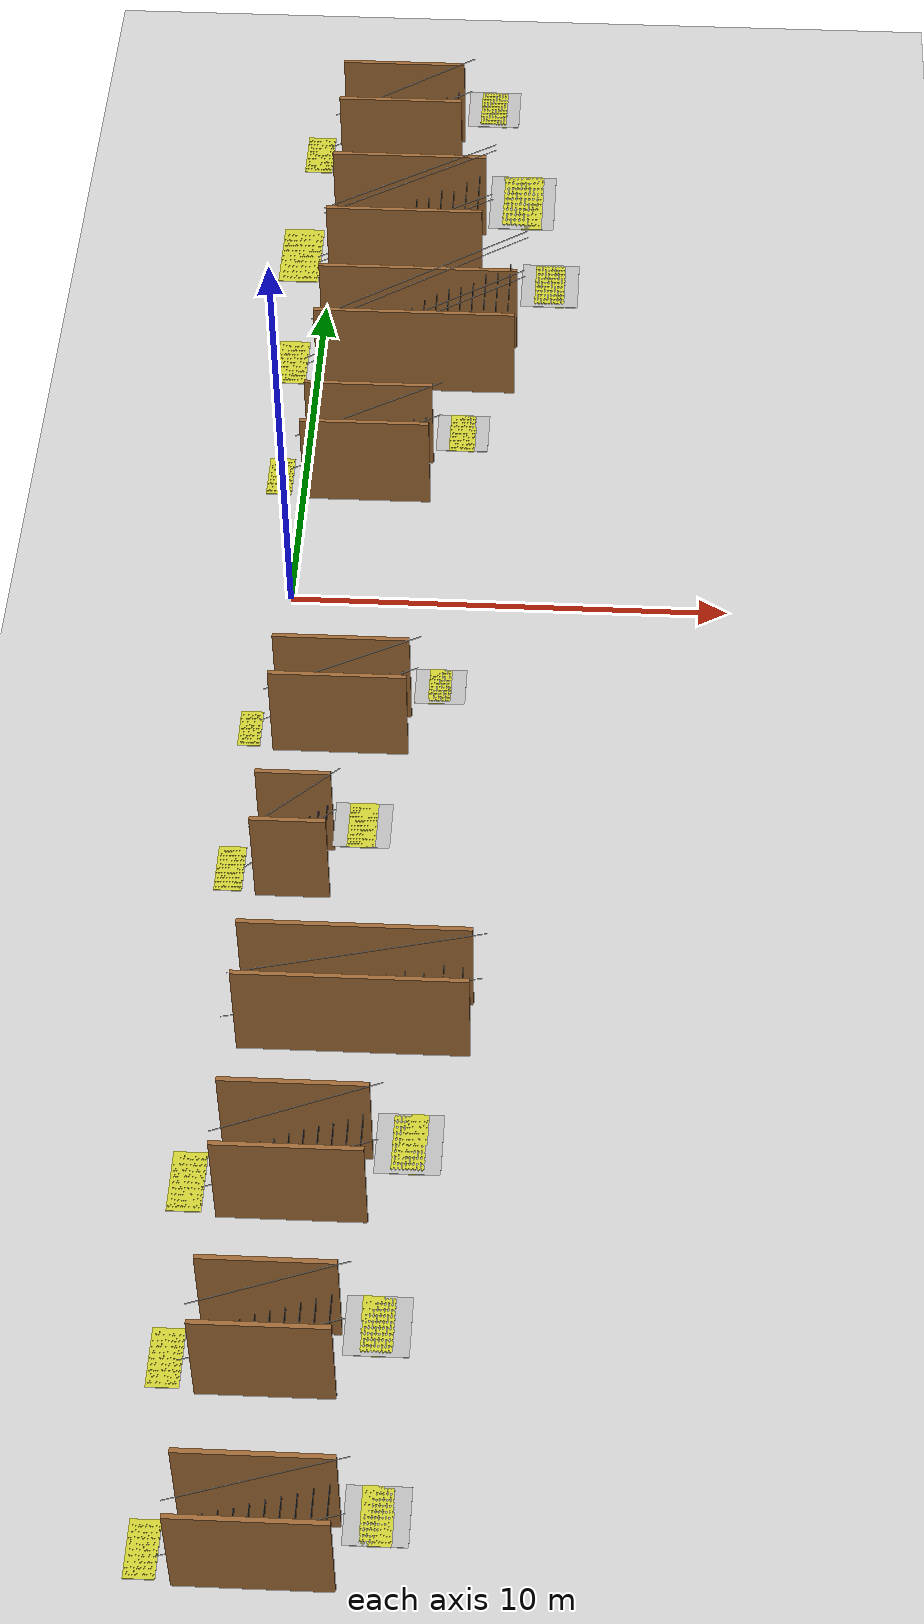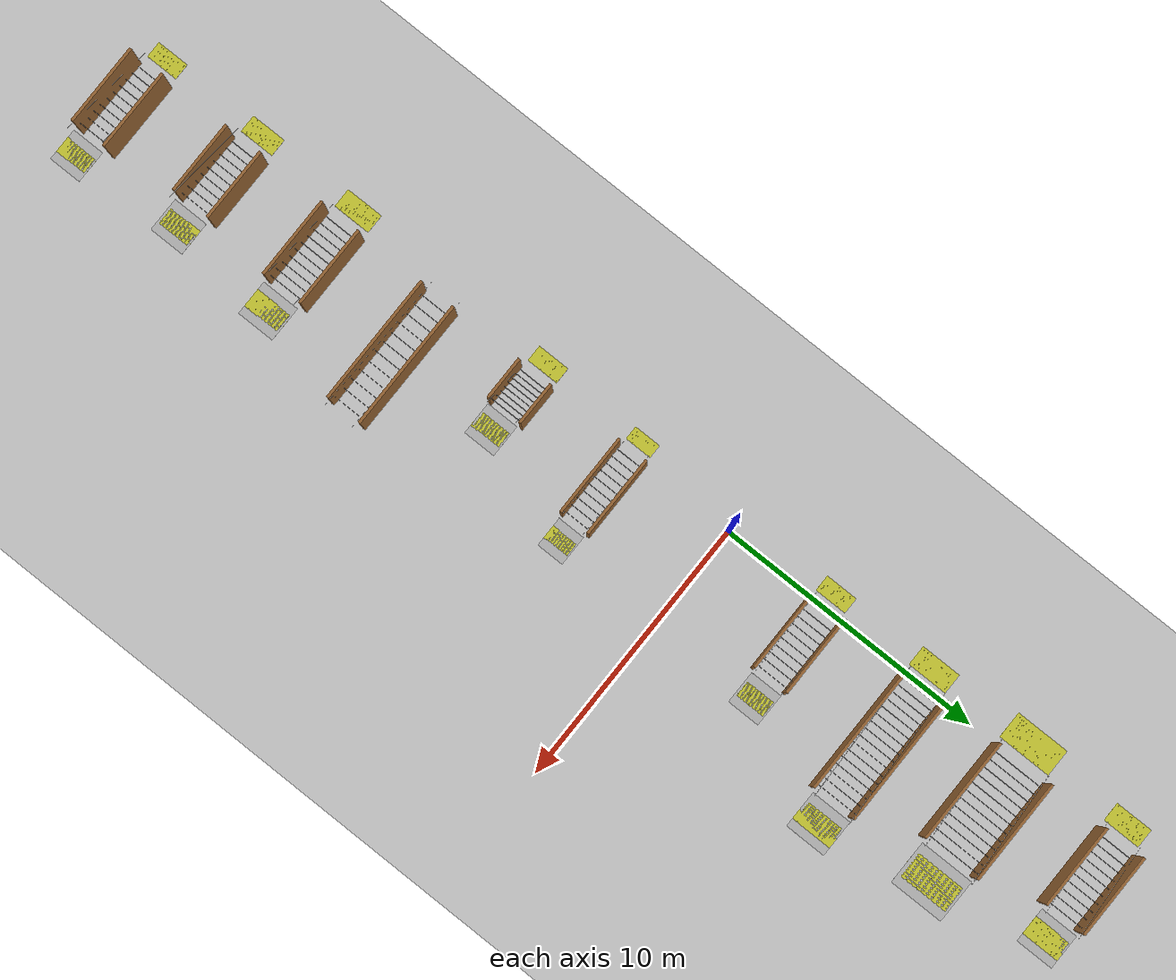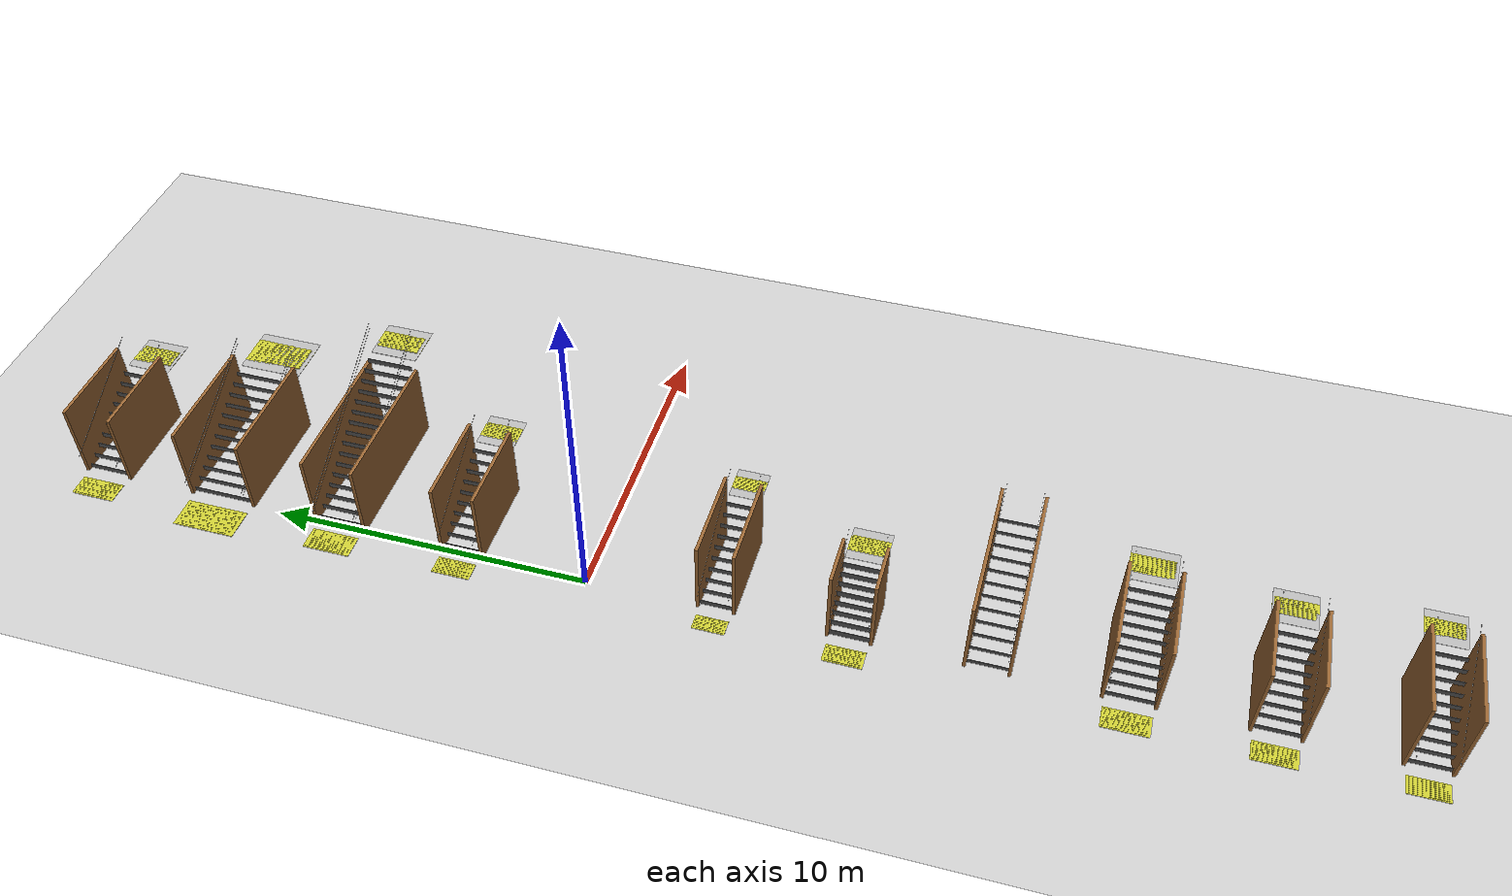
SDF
<sdf version="1.7">
 <world name="default">
  <include><uri>https://fuel.gazebosim.org/1.0/openrobotics/models/Ground%20Plane</uri></include>
  <include><uri>https://fuel.gazebosim.org/1.0/openrobotics/models/Sun</uri></include>
  <model name="tactile_strip_tactile_strip_before_2380114d-61c0-4db8-95cd-3a11f1002797_8a8556f7-3a6e-456c-b705-32682d6e687a">
   <static>true</static>
   <pose>-0.6 4.0 0.0 0 0 0</pose>
   <link name="link">
    <visual name="visual">
     <geometry>
      <mesh><uri>model://data/world-generator/assets/tactile_strip_unit.stl</uri><scale>0.6 1.2 1</scale></mesh>
     </geometry>
     <material><ambient>0.8 0.8 0.2 1</ambient><diffuse>0.8 0.8 0.2 1</diffuse></material>
    </visual>
    <collision name="collision"><geometry><box><size>0.6 1.2 0.02</size></box></geometry></collision>
   </link>
  </model>
  <model name="tactile_strip_tactile_strip_after_2380114d-61c0-4db8-95cd-3a11f1002797_c2bafa8b-1b6a-454e-ac4f-f03ee88ef546">
   <static>true</static>
   <pose>3.749999999999999 4.0 1.5999999999999999 0 0 0</pose>
   <link name="link">
    <visual name="visual">
     <geometry>
      <mesh><uri>model://data/world-generator/assets/tactile_strip_unit.stl</uri><scale>0.6 1.2 1</scale></mesh>
     </geometry>
     <material><ambient>0.8 0.8 0.2 1</ambient><diffuse>0.8 0.8 0.2 1</diffuse></material>
    </visual>
    <collision name="collision"><geometry><box><size>0.6 1.2 0.02</size></box></geometry></collision>
   </link>
  </model>
  <model name="handrail_handrail_2380114d-61c0-4db8-95cd-3a11f1002797_{'height': 0.95, 'extension_length': 0.3, 'offset_from_wall': 0.04}_dd895d16-0f13-45a6-bb25-cd8e64cd3b47">
   <static>true</static>
   <pose>1.5 3.44 1.75 0 -0.48995732625372834 0</pose>
   <link name="link">
    <visual name="visual">
     <geometry>
      <mesh><uri>model://data/world-generator/assets/handrail_unit.stl</uri><scale>4.0 0.25 0.95</scale></mesh>
     </geometry>
     <material><ambient>0.7 0.7 0.7 1</ambient><diffuse>0.7 0.7 0.7 1</diffuse></material>
    </visual>
    <collision name="collision">
     <geometry><cylinder><radius>0.125</radius><length>4.0</length></cylinder></geometry>
    </collision>
   </link>
  </model>
  <model name="handrail_handrail_2380114d-61c0-4db8-95cd-3a11f1002797_{'height': 0.95, 'extension_length': 0.3, 'offset_from_wall': 0.04}_a3f463f3-668c-4367-9701-24da02bdedce">
   <static>true</static>
   <pose>1.5 4.56 1.75 0 -0.48995732625372834 0</pose>
   <link name="link">
    <visual name="visual">
     <geometry>
      <mesh><uri>model://data/world-generator/assets/handrail_unit.stl</uri><scale>4.0 0.25 0.95</scale></mesh>
     </geometry>
     <material><ambient>0.7 0.7 0.7 1</ambient><diffuse>0.7 0.7 0.7 1</diffuse></material>
    </visual>
    <collision name="collision">
     <geometry><cylinder><radius>0.125</radius><length>4.0</length></cylinder></geometry>
    </collision>
   </link>
  </model>
  <model name="riser_riser_0f4c67bf-021a-45f8-92c6-092875decb3c_0b168ed3-7ea6-4166-9fbf-4b085acc85c7">
   <static>true</static>
   <pose>0.15 4.0 0.0 0 0 0</pose>
   <link name="link">
    <visual name="visual">
     <geometry>
      <mesh><uri>model://data/world-generator/assets/riser_unit.stl</uri><scale>1 1.2 0.16</scale></mesh>
     </geometry>
     <material><ambient>0.3 0.3 0.3 1</ambient><diffuse>0.3 0.3 0.3 1</diffuse></material>
    </visual>
    <collision name="collision"><geometry><box><size>0.01 1.2 0.16</size></box></geometry></collision>
   </link>
  </model>
  <model name="riser_riser_56ba4ca1-7edb-4753-bffd-d643aa920a7e_2e5eaf9a-eeb9-49a0-b7e6-5f50fb1637c4">
   <static>true</static>
   <pose>0.44999999999999996 4.0 0.16 0 0 0</pose>
   <link name="link">
    <visual name="visual">
     <geometry>
      <mesh><uri>model://data/world-generator/assets/riser_unit.stl</uri><scale>1 1.2 0.16</scale></mesh>
     </geometry>
     <material><ambient>0.3 0.3 0.3 1</ambient><diffuse>0.3 0.3 0.3 1</diffuse></material>
    </visual>
    <collision name="collision"><geometry><box><size>0.01 1.2 0.16</size></box></geometry></collision>
   </link>
  </model>
  <model name="riser_riser_aa39482c-cc10-46a6-8c8d-65e14d5c979c_4f6b79d0-e20d-4615-96da-080c0f4155cb">
   <static>true</static>
   <pose>0.75 4.0 0.32 0 0 0</pose>
   <link name="link">
    <visual name="visual">
     <geometry>
      <mesh><uri>model://data/world-generator/assets/riser_unit.stl</uri><scale>1 1.2 0.16</scale></mesh>
     </geometry>
     <material><ambient>0.3 0.3 0.3 1</ambient><diffuse>0.3 0.3 0.3 1</diffuse></material>
    </visual>
    <collision name="collision"><geometry><box><size>0.01 1.2 0.16</size></box></geometry></collision>
   </link>
  </model>
  <model name="riser_riser_aef47aba-85f2-47a9-a8ad-6f19306f6455_f2d67954-2f8a-49c9-b6d3-07291a93f0e0">
   <static>true</static>
   <pose>1.05 4.0 0.48 0 0 0</pose>
   <link name="link">
    <visual name="visual">
     <geometry>
      <mesh><uri>model://data/world-generator/assets/riser_unit.stl</uri><scale>1 1.2 0.16</scale></mesh>
     </geometry>
     <material><ambient>0.3 0.3 0.3 1</ambient><diffuse>0.3 0.3 0.3 1</diffuse></material>
    </visual>
    <collision name="collision"><geometry><box><size>0.01 1.2 0.16</size></box></geometry></collision>
   </link>
  </model>
  <model name="riser_riser_650e838f-bc9c-4ae9-829d-48057fdc0816_bafde185-910b-4c3f-a148-b1685ad74749">
   <static>true</static>
   <pose>1.35 4.0 0.64 0 0 0</pose>
   <link name="link">
    <visual name="visual">
     <geometry>
      <mesh><uri>model://data/world-generator/assets/riser_unit.stl</uri><scale>1 1.2 0.16</scale></mesh>
     </geometry>
     <material><ambient>0.3 0.3 0.3 1</ambient><diffuse>0.3 0.3 0.3 1</diffuse></material>
    </visual>
    <collision name="collision"><geometry><box><size>0.01 1.2 0.16</size></box></geometry></collision>
   </link>
  </model>
  <model name="riser_riser_a17315cc-52c6-4d6a-b655-59889c3cf503_74edd328-1a46-45c3-be21-85d3eb1bb8e6">
   <static>true</static>
   <pose>1.6500000000000001 4.0 0.8 0 0 0</pose>
   <link name="link">
    <visual name="visual">
     <geometry>
      <mesh><uri>model://data/world-generator/assets/riser_unit.stl</uri><scale>1 1.2 0.16</scale></mesh>
     </geometry>
     <material><ambient>0.3 0.3 0.3 1</ambient><diffuse>0.3 0.3 0.3 1</diffuse></material>
    </visual>
    <collision name="collision"><geometry><box><size>0.01 1.2 0.16</size></box></geometry></collision>
   </link>
  </model>
  <model name="riser_riser_0e743970-89c8-4c1c-b477-505d78edf11f_32cb2962-36df-4b33-b5bc-f68f71a99067">
   <static>true</static>
   <pose>1.9500000000000002 4.0 0.9600000000000001 0 0 0</pose>
   <link name="link">
    <visual name="visual">
     <geometry>
      <mesh><uri>model://data/world-generator/assets/riser_unit.stl</uri><scale>1 1.2 0.16</scale></mesh>
     </geometry>
     <material><ambient>0.3 0.3 0.3 1</ambient><diffuse>0.3 0.3 0.3 1</diffuse></material>
    </visual>
    <collision name="collision"><geometry><box><size>0.01 1.2 0.16</size></box></geometry></collision>
   </link>
  </model>
  <model name="riser_riser_ee1d7364-8cf7-4684-8c33-de820b228c25_21e7b03e-a898-4749-81aa-2e965841548e">
   <static>true</static>
   <pose>2.25 4.0 1.12 0 0 0</pose>
   <link name="link">
    <visual name="visual">
     <geometry>
      <mesh><uri>model://data/world-generator/assets/riser_unit.stl</uri><scale>1 1.2 0.16</scale></mesh>
     </geometry>
     <material><ambient>0.3 0.3 0.3 1</ambient><diffuse>0.3 0.3 0.3 1</diffuse></material>
    </visual>
    <collision name="collision"><geometry><box><size>0.01 1.2 0.16</size></box></geometry></collision>
   </link>
  </model>
  <model name="riser_riser_8e4c708e-b4e6-4325-8917-a5818f8687a9_7c611999-69f5-4d79-bab2-1ccb9a942b64">
   <static>true</static>
   <pose>2.55 4.0 1.28 0 0 0</pose>
   <link name="link">
    <visual name="visual">
     <geometry>
      <mesh><uri>model://data/world-generator/assets/riser_unit.stl</uri><scale>1 1.2 0.16</scale></mesh>
     </geometry>
     <material><ambient>0.3 0.3 0.3 1</ambient><diffuse>0.3 0.3 0.3 1</diffuse></material>
    </visual>
    <collision name="collision"><geometry><box><size>0.01 1.2 0.16</size></box></geometry></collision>
   </link>
  </model>
  <model name="riser_riser_4d2f33eb-3987-4c9b-b705-4a46a4b2c9cc_3a343302-66c3-4624-9ba4-09040606d264">
   <static>true</static>
   <pose>2.8499999999999996 4.0 1.44 0 0 0</pose>
   <link name="link">
    <visual name="visual">
     <geometry>
      <mesh><uri>model://data/world-generator/assets/riser_unit.stl</uri><scale>1 1.2 0.16</scale></mesh>
     </geometry>
     <material><ambient>0.3 0.3 0.3 1</ambient><diffuse>0.3 0.3 0.3 1</diffuse></material>
    </visual>
    <collision name="collision"><geometry><box><size>0.01 1.2 0.16</size></box></geometry></collision>
   </link>
  </model>
  <model name="wall_staircase_1_left_fc63aef7-f557-46f6-b317-942239e3bee1">
   <static>true</static>
   <pose>1.5 3.35 0.0 0 0 0.0</pose>
   <link name="link">
    <visual name="visual">
     <geometry>
      <mesh><uri>model://data/world-generator/assets/wall_unit.stl</uri><scale>3.0 1 1</scale></mesh>
     </geometry>
     <material><ambient>0.6 0.4 0.2 1</ambient><diffuse>0.6 0.4 0.2 1</diffuse></material>
    </visual>
    <collision name="collision"><geometry><box><size>3.0 0.1 1.2</size></box></geometry></collision>
   </link>
  </model>
  <model name="wall_staircase_1_right_12936ddd-f6f5-4d0c-b6a4-6eaac51be5f9">
   <static>true</static>
   <pose>1.5 4.6499999999999995 0.0 0 0 0.0</pose>
   <link name="link">
    <visual name="visual">
     <geometry>
      <mesh><uri>model://data/world-generator/assets/wall_unit.stl</uri><scale>3.0 1 1</scale></mesh>
     </geometry>
     <material><ambient>0.6 0.4 0.2 1</ambient><diffuse>0.6 0.4 0.2 1</diffuse></material>
    </visual>
    <collision name="collision"><geometry><box><size>3.0 0.1 1.2</size></box></geometry></collision>
   </link>
  </model>
  <model name="platform_staircase_1_landing_359a9a06-f22f-4184-8473-b10db1d0b27e">
   <static>true</static>
   <pose>3.749999999999999 4.0 1.5999999999999999 0 0 0</pose>
   <link name="link">
    <visual name="visual">
     <geometry>
      <mesh><uri>model://data/world-generator/assets/platform_unit.stl</uri><scale>1.2 1.2 1</scale></mesh>
     </geometry>
    </visual>
    <collision name="collision"><geometry><box><size>1.2 1.2 0.01</size></box></geometry></collision>
   </link>
  </model>
  <model name="tactile_strip_tactile_strip_before_e99f2752-ab1f-4d2a-a1d9-9a706f787795_b9c07315-d704-40d7-b5e5-395025c992d8">
   <static>true</static>
   <pose>-0.675 8.0 0.0 0 0 0</pose>
   <link name="link">
    <visual name="visual">
     <geometry>
      <mesh><uri>model://data/world-generator/assets/tactile_strip_unit.stl</uri><scale>0.75 1.5 1</scale></mesh>
     </geometry>
     <material><ambient>0.8 0.8 0.2 1</ambient><diffuse>0.8 0.8 0.2 1</diffuse></material>
    </visual>
    <collision name="collision"><geometry><box><size>0.75 1.5 0.02</size></box></geometry></collision>
   </link>
  </model>
  <model name="tactile_strip_tactile_strip_after_e99f2752-ab1f-4d2a-a1d9-9a706f787795_514fd597-a8f3-4561-81c5-7cfd90c532dc">
   <static>true</static>
   <pose>5.624999999999998 8.0 2.7199999999999993 0 0 0</pose>
   <link name="link">
    <visual name="visual">
     <geometry>
      <mesh><uri>model://data/world-generator/assets/tactile_strip_unit.stl</uri><scale>0.75 1.5 1</scale></mesh>
     </geometry>
     <material><ambient>0.8 0.8 0.2 1</ambient><diffuse>0.8 0.8 0.2 1</diffuse></material>
    </visual>
    <collision name="collision"><geometry><box><size>0.75 1.5 0.02</size></box></geometry></collision>
   </link>
  </model>
  <model name="handrail_handrail_e99f2752-ab1f-4d2a-a1d9-9a706f787795_{'height': 0.95, 'extension_length': 0.3, 'offset_from_wall': 0.05}_4281d745-f4f5-41e8-b2f1-ba8e8f079b40">
   <static>true</static>
   <pose>2.4 7.3 2.31 0 -0.5155490074589791 0</pose>
   <link name="link">
    <visual name="visual">
     <geometry>
      <mesh>
       <uri>model://data/world-generator/assets/handrail_unit.stl</uri>
       <scale>6.117100687861333 0.25 0.95</scale>
      </mesh>
     </geometry>
     <material><ambient>0.7 0.7 0.7 1</ambient><diffuse>0.7 0.7 0.7 1</diffuse></material>
    </visual>
    <collision name="collision">
     <geometry><cylinder><radius>0.125</radius><length>6.117100687861333</length></cylinder></geometry>
    </collision>
   </link>
  </model>
  <model name="handrail_handrail_e99f2752-ab1f-4d2a-a1d9-9a706f787795_{'height': 0.95, 'extension_length': 0.3, 'offset_from_wall': 0.05}_4e0cbe52-9989-4e63-aa49-a05e3eff6bc6">
   <static>true</static>
   <pose>2.4 8.7 2.31 0 -0.5155490074589791 0</pose>
   <link name="link">
    <visual name="visual">
     <geometry>
      <mesh>
       <uri>model://data/world-generator/assets/handrail_unit.stl</uri>
       <scale>6.117100687861333 0.25 0.95</scale>
      </mesh>
     </geometry>
     <material><ambient>0.7 0.7 0.7 1</ambient><diffuse>0.7 0.7 0.7 1</diffuse></material>
    </visual>
    <collision name="collision">
     <geometry><cylinder><radius>0.125</radius><length>6.117100687861333</length></cylinder></geometry>
    </collision>
   </link>
  </model>
  <model name="handrail_handrail_e99f2752-ab1f-4d2a-a1d9-9a706f787795_{'height': 0.75, 'extension_length': 0.3, 'offset_from_wall': 0.05}_4aece168-5643-4394-8c12-1170bd99f4e0">
   <static>true</static>
   <pose>2.4 7.3 2.1100000000000003 0 -0.5155490074589791 0</pose>
   <link name="link">
    <visual name="visual">
     <geometry>
      <mesh>
       <uri>model://data/world-generator/assets/handrail_unit.stl</uri>
       <scale>6.117100687861333 0.25 0.75</scale>
      </mesh>
     </geometry>
     <material><ambient>0.7 0.7 0.7 1</ambient><diffuse>0.7 0.7 0.7 1</diffuse></material>
    </visual>
    <collision name="collision">
     <geometry><cylinder><radius>0.125</radius><length>6.117100687861333</length></cylinder></geometry>
    </collision>
   </link>
  </model>
  <model name="handrail_handrail_e99f2752-ab1f-4d2a-a1d9-9a706f787795_{'height': 0.75, 'extension_length': 0.3, 'offset_from_wall': 0.05}_c0779a72-7dce-4da5-b469-8b89622a1f1a">
   <static>true</static>
   <pose>2.4 8.7 2.1100000000000003 0 -0.5155490074589791 0</pose>
   <link name="link">
    <visual name="visual">
     <geometry>
      <mesh>
       <uri>model://data/world-generator/assets/handrail_unit.stl</uri>
       <scale>6.117100687861333 0.25 0.75</scale>
      </mesh>
     </geometry>
     <material><ambient>0.7 0.7 0.7 1</ambient><diffuse>0.7 0.7 0.7 1</diffuse></material>
    </visual>
    <collision name="collision">
     <geometry><cylinder><radius>0.125</radius><length>6.117100687861333</length></cylinder></geometry>
    </collision>
   </link>
  </model>
  <model name="riser_riser_9279e2e1-6e9f-4bb0-81bc-6a40666967ec_043a1877-ea40-40bc-ae3c-dd26e49cc3e2">
   <static>true</static>
   <pose>0.15 8.0 0.0 0 0 0</pose>
   <link name="link">
    <visual name="visual">
     <geometry>
      <mesh><uri>model://data/world-generator/assets/riser_unit.stl</uri><scale>1 1.5 0.17</scale></mesh>
     </geometry>
     <material><ambient>0.3 0.3 0.3 1</ambient><diffuse>0.3 0.3 0.3 1</diffuse></material>
    </visual>
    <collision name="collision"><geometry><box><size>0.01 1.5 0.17</size></box></geometry></collision>
   </link>
  </model>
  <model name="riser_riser_a43ab379-733a-400a-8d28-5ad033e78ae4_2ded8f81-8b93-46ff-9e88-c8a0ccf28432">
   <static>true</static>
   <pose>0.44999999999999996 8.0 0.17 0 0 0</pose>
   <link name="link">
    <visual name="visual">
     <geometry>
      <mesh><uri>model://data/world-generator/assets/riser_unit.stl</uri><scale>1 1.5 0.17</scale></mesh>
     </geometry>
     <material><ambient>0.3 0.3 0.3 1</ambient><diffuse>0.3 0.3 0.3 1</diffuse></material>
    </visual>
    <collision name="collision"><geometry><box><size>0.01 1.5 0.17</size></box></geometry></collision>
   </link>
  </model>
  <model name="riser_riser_f6267ff2-eea4-447a-8004-f271e1d8e42b_fa8ed3f1-3ff9-4700-8cf1-3847c70e3324">
   <static>true</static>
   <pose>0.75 8.0 0.34 0 0 0</pose>
   <link name="link">
    <visual name="visual">
     <geometry>
      <mesh><uri>model://data/world-generator/assets/riser_unit.stl</uri><scale>1 1.5 0.17</scale></mesh>
     </geometry>
     <material><ambient>0.3 0.3 0.3 1</ambient><diffuse>0.3 0.3 0.3 1</diffuse></material>
    </visual>
    <collision name="collision"><geometry><box><size>0.01 1.5 0.17</size></box></geometry></collision>
   </link>
  </model>
  <model name="riser_riser_685879c6-fb81-41a2-a4d1-3b52f1c5dab6_7fd22378-8c4c-460a-b61f-0bb088b6a48c">
   <static>true</static>
   <pose>1.05 8.0 0.51 0 0 0</pose>
   <link name="link">
    <visual name="visual">
     <geometry>
      <mesh><uri>model://data/world-generator/assets/riser_unit.stl</uri><scale>1 1.5 0.17</scale></mesh>
     </geometry>
     <material><ambient>0.3 0.3 0.3 1</ambient><diffuse>0.3 0.3 0.3 1</diffuse></material>
    </visual>
    <collision name="collision"><geometry><box><size>0.01 1.5 0.17</size></box></geometry></collision>
   </link>
  </model>
  <model name="riser_riser_40349897-c3ab-4b66-9dcf-2767a300302b_2c7cd6ee-ca1e-4143-b250-db4054511e5a">
   <static>true</static>
   <pose>1.35 8.0 0.68 0 0 0</pose>
   <link name="link">
    <visual name="visual">
     <geometry>
      <mesh><uri>model://data/world-generator/assets/riser_unit.stl</uri><scale>1 1.5 0.17</scale></mesh>
     </geometry>
     <material><ambient>0.3 0.3 0.3 1</ambient><diffuse>0.3 0.3 0.3 1</diffuse></material>
    </visual>
    <collision name="collision"><geometry><box><size>0.01 1.5 0.17</size></box></geometry></collision>
   </link>
  </model>
  <model name="riser_riser_d326e7a7-658c-4800-a5f3-da62ebdc0ae2_8bf8be7a-5fbd-45b1-b0d9-92574366be86">
   <static>true</static>
   <pose>1.6500000000000001 8.0 0.8500000000000001 0 0 0</pose>
   <link name="link">
    <visual name="visual">
     <geometry>
      <mesh><uri>model://data/world-generator/assets/riser_unit.stl</uri><scale>1 1.5 0.17</scale></mesh>
     </geometry>
     <material><ambient>0.3 0.3 0.3 1</ambient><diffuse>0.3 0.3 0.3 1</diffuse></material>
    </visual>
    <collision name="collision"><geometry><box><size>0.01 1.5 0.17</size></box></geometry></collision>
   </link>
  </model>
  <model name="riser_riser_106647b5-8b85-4093-895f-2d1a50ac950b_bd218183-47c5-4515-9107-e2ebf88c227e">
   <static>true</static>
   <pose>1.9500000000000002 8.0 1.02 0 0 0</pose>
   <link name="link">
    <visual name="visual">
     <geometry>
      <mesh><uri>model://data/world-generator/assets/riser_unit.stl</uri><scale>1 1.5 0.17</scale></mesh>
     </geometry>
     <material><ambient>0.3 0.3 0.3 1</ambient><diffuse>0.3 0.3 0.3 1</diffuse></material>
    </visual>
    <collision name="collision"><geometry><box><size>0.01 1.5 0.17</size></box></geometry></collision>
   </link>
  </model>
  <model name="riser_riser_70d5e60e-101b-49a8-9775-bf4cb220a134_5b0fa1b0-189c-4769-bbe2-bc9fa8a426d7">
   <static>true</static>
   <pose>2.25 8.0 1.19 0 0 0</pose>
   <link name="link">
    <visual name="visual">
     <geometry>
      <mesh><uri>model://data/world-generator/assets/riser_unit.stl</uri><scale>1 1.5 0.17</scale></mesh>
     </geometry>
     <material><ambient>0.3 0.3 0.3 1</ambient><diffuse>0.3 0.3 0.3 1</diffuse></material>
    </visual>
    <collision name="collision"><geometry><box><size>0.01 1.5 0.17</size></box></geometry></collision>
   </link>
  </model>
  <model name="riser_riser_7f58af73-5285-4088-8d29-ced0b5c631ed_1576f5b9-5923-4c76-a85a-d97effd3f1ce">
   <static>true</static>
   <pose>2.55 8.0 1.3599999999999999 0 0 0</pose>
   <link name="link">
    <visual name="visual">
     <geometry>
      <mesh><uri>model://data/world-generator/assets/riser_unit.stl</uri><scale>1 1.5 0.17</scale></mesh>
     </geometry>
     <material><ambient>0.3 0.3 0.3 1</ambient><diffuse>0.3 0.3 0.3 1</diffuse></material>
    </visual>
    <collision name="collision"><geometry><box><size>0.01 1.5 0.17</size></box></geometry></collision>
   </link>
  </model>
  <model name="riser_riser_e186d29a-a671-4bb2-af89-5989b9bc7903_474552ea-487b-4f61-9c23-02fbe9d76db0">
   <static>true</static>
   <pose>2.8499999999999996 8.0 1.5299999999999998 0 0 0</pose>
   <link name="link">
    <visual name="visual">
     <geometry>
      <mesh><uri>model://data/world-generator/assets/riser_unit.stl</uri><scale>1 1.5 0.17</scale></mesh>
     </geometry>
     <material><ambient>0.3 0.3 0.3 1</ambient><diffuse>0.3 0.3 0.3 1</diffuse></material>
    </visual>
    <collision name="collision"><geometry><box><size>0.01 1.5 0.17</size></box></geometry></collision>
   </link>
  </model>
  <model name="riser_riser_8a2d66bd-610a-4c22-898d-7c5158cfe98a_7b48eccf-0824-4db7-b37e-d10716b933ae">
   <static>true</static>
   <pose>3.1499999999999995 8.0 1.6999999999999997 0 0 0</pose>
   <link name="link">
    <visual name="visual">
     <geometry>
      <mesh><uri>model://data/world-generator/assets/riser_unit.stl</uri><scale>1 1.5 0.17</scale></mesh>
     </geometry>
     <material><ambient>0.3 0.3 0.3 1</ambient><diffuse>0.3 0.3 0.3 1</diffuse></material>
    </visual>
    <collision name="collision"><geometry><box><size>0.01 1.5 0.17</size></box></geometry></collision>
   </link>
  </model>
  <model name="riser_riser_408af33a-df1b-4398-ba9f-c0f7def514e7_bfa01fc2-e137-41ef-a7ac-d5e229311a45">
   <static>true</static>
   <pose>3.4499999999999993 8.0 1.8699999999999997 0 0 0</pose>
   <link name="link">
    <visual name="visual">
     <geometry>
      <mesh><uri>model://data/world-generator/assets/riser_unit.stl</uri><scale>1 1.5 0.17</scale></mesh>
     </geometry>
     <material><ambient>0.3 0.3 0.3 1</ambient><diffuse>0.3 0.3 0.3 1</diffuse></material>
    </visual>
    <collision name="collision"><geometry><box><size>0.01 1.5 0.17</size></box></geometry></collision>
   </link>
  </model>
  <model name="riser_riser_41ccc42d-1cc5-4bfa-9c6c-4adf6c871611_fe7c1311-df24-4163-a91f-0cc55218e23f">
   <static>true</static>
   <pose>3.749999999999999 8.0 2.0399999999999996 0 0 0</pose>
   <link name="link">
    <visual name="visual">
     <geometry>
      <mesh><uri>model://data/world-generator/assets/riser_unit.stl</uri><scale>1 1.5 0.17</scale></mesh>
     </geometry>
     <material><ambient>0.3 0.3 0.3 1</ambient><diffuse>0.3 0.3 0.3 1</diffuse></material>
    </visual>
    <collision name="collision"><geometry><box><size>0.01 1.5 0.17</size></box></geometry></collision>
   </link>
  </model>
  <model name="riser_riser_0e819c5d-6a93-46c0-a9ff-613c3ab32ddb_d1b86434-2ce1-4829-97a3-e57eea6dc603">
   <static>true</static>
   <pose>4.049999999999999 8.0 2.2099999999999995 0 0 0</pose>
   <link name="link">
    <visual name="visual">
     <geometry>
      <mesh><uri>model://data/world-generator/assets/riser_unit.stl</uri><scale>1 1.5 0.17</scale></mesh>
     </geometry>
     <material><ambient>0.3 0.3 0.3 1</ambient><diffuse>0.3 0.3 0.3 1</diffuse></material>
    </visual>
    <collision name="collision"><geometry><box><size>0.01 1.5 0.17</size></box></geometry></collision>
   </link>
  </model>
  <model name="riser_riser_8ed4610e-6e04-4517-a38a-cca709721bdd_89f0c0a3-1fd0-4cf4-a1f5-6c6990491fa8">
   <static>true</static>
   <pose>4.349999999999999 8.0 2.3799999999999994 0 0 0</pose>
   <link name="link">
    <visual name="visual">
     <geometry>
      <mesh><uri>model://data/world-generator/assets/riser_unit.stl</uri><scale>1 1.5 0.17</scale></mesh>
     </geometry>
     <material><ambient>0.3 0.3 0.3 1</ambient><diffuse>0.3 0.3 0.3 1</diffuse></material>
    </visual>
    <collision name="collision"><geometry><box><size>0.01 1.5 0.17</size></box></geometry></collision>
   </link>
  </model>
  <model name="riser_riser_68b2cc15-30e8-4c36-a15a-e7701679fc83_7f7ccbd5-ee7b-43f9-9608-7ec573315ec1">
   <static>true</static>
   <pose>4.649999999999999 8.0 2.5499999999999994 0 0 0</pose>
   <link name="link">
    <visual name="visual">
     <geometry>
      <mesh><uri>model://data/world-generator/assets/riser_unit.stl</uri><scale>1 1.5 0.17</scale></mesh>
     </geometry>
     <material><ambient>0.3 0.3 0.3 1</ambient><diffuse>0.3 0.3 0.3 1</diffuse></material>
    </visual>
    <collision name="collision"><geometry><box><size>0.01 1.5 0.17</size></box></geometry></collision>
   </link>
  </model>
  <model name="wall_stairs_single_flight_left_f1f274e6-447f-40af-b96e-c4f48927b3f7">
   <static>true</static>
   <pose>2.4 7.2 0.0 0 0 0.0</pose>
   <link name="link">
    <visual name="visual">
     <geometry>
      <mesh><uri>model://data/world-generator/assets/wall_unit.stl</uri><scale>4.8 1 1</scale></mesh>
     </geometry>
     <material><ambient>0.6 0.4 0.2 1</ambient><diffuse>0.6 0.4 0.2 1</diffuse></material>
    </visual>
    <collision name="collision"><geometry><box><size>4.8 0.1 1.2</size></box></geometry></collision>
   </link>
  </model>
  <model name="wall_stairs_single_flight_right_8a9d1c2e-b309-403f-81af-117c11bf0747">
   <static>true</static>
   <pose>2.4 8.8 0.0 0 0 0.0</pose>
   <link name="link">
    <visual name="visual">
     <geometry>
      <mesh><uri>model://data/world-generator/assets/wall_unit.stl</uri><scale>4.8 1 1</scale></mesh>
     </geometry>
     <material><ambient>0.6 0.4 0.2 1</ambient><diffuse>0.6 0.4 0.2 1</diffuse></material>
    </visual>
    <collision name="collision"><geometry><box><size>4.8 0.1 1.2</size></box></geometry></collision>
   </link>
  </model>
  <model name="platform_stairs_single_flight_landing_e4347f66-9b4a-4370-9b18-dd551f726a3b">
   <static>true</static>
   <pose>5.624999999999998 8.0 2.7199999999999993 0 0 0</pose>
   <link name="link">
    <visual name="visual">
     <geometry>
      <mesh><uri>model://data/world-generator/assets/platform_unit.stl</uri><scale>1.35 1.5 1</scale></mesh>
     </geometry>
    </visual>
    <collision name="collision"><geometry><box><size>1.35 1.5 0.01</size></box></geometry></collision>
   </link>
  </model>
  <model name="tactile_strip_tactile_strip_before_817106a5-c30b-49ad-9c9e-73a6f7a4562b_079eb2d5-0e05-4f57-b725-a9f4de5cbb58">
   <static>true</static>
   <pose>-0.8 12.0 0.0 0 0 0</pose>
   <link name="link">
    <visual name="visual">
     <geometry>
      <mesh><uri>model://data/world-generator/assets/tactile_strip_unit.stl</uri><scale>1.0 2.0 1</scale></mesh>
     </geometry>
     <material><ambient>0.8 0.8 0.2 1</ambient><diffuse>0.8 0.8 0.2 1</diffuse></material>
    </visual>
    <collision name="collision"><geometry><box><size>1.0 2.0 0.02</size></box></geometry></collision>
   </link>
  </model>
  <model name="tactile_strip_tactile_strip_after_817106a5-c30b-49ad-9c9e-73a6f7a4562b_f385c036-54c2-42f3-a181-c4ce01cb619b">
   <static>true</static>
   <pose>4.799999999999999 12.0 1.9199999999999997 0 0 0</pose>
   <link name="link">
    <visual name="visual">
     <geometry>
      <mesh><uri>model://data/world-generator/assets/tactile_strip_unit.stl</uri><scale>1.0 2.0 1</scale></mesh>
     </geometry>
     <material><ambient>0.8 0.8 0.2 1</ambient><diffuse>0.8 0.8 0.2 1</diffuse></material>
    </visual>
    <collision name="collision"><geometry><box><size>1.0 2.0 0.02</size></box></geometry></collision>
   </link>
  </model>
  <model name="handrail_handrail_817106a5-c30b-49ad-9c9e-73a6f7a4562b_{'height': 0.92, 'extension_length': 0.3, 'offset_from_wall': 0.05}_a5023ef4-65f4-4ebd-9fd3-0c7590a298f1">
   <static>true</static>
   <pose>1.92 11.05 1.88 0 -0.4636476090008061 0</pose>
   <link name="link">
    <visual name="visual">
     <geometry>
      <mesh>
       <uri>model://data/world-generator/assets/handrail_unit.stl</uri>
       <scale>4.893250516799596 0.25 0.92</scale>
      </mesh>
     </geometry>
     <material><ambient>0.7 0.7 0.7 1</ambient><diffuse>0.7 0.7 0.7 1</diffuse></material>
    </visual>
    <collision name="collision">
     <geometry><cylinder><radius>0.125</radius><length>4.893250516799596</length></cylinder></geometry>
    </collision>
   </link>
  </model>
  <model name="handrail_handrail_817106a5-c30b-49ad-9c9e-73a6f7a4562b_{'height': 0.92, 'extension_length': 0.3, 'offset_from_wall': 0.05}_169be045-e5ca-420a-96e6-f7e57d24af40">
   <static>true</static>
   <pose>1.92 12.95 1.88 0 -0.4636476090008061 0</pose>
   <link name="link">
    <visual name="visual">
     <geometry>
      <mesh>
       <uri>model://data/world-generator/assets/handrail_unit.stl</uri>
       <scale>4.893250516799596 0.25 0.92</scale>
      </mesh>
     </geometry>
     <material><ambient>0.7 0.7 0.7 1</ambient><diffuse>0.7 0.7 0.7 1</diffuse></material>
    </visual>
    <collision name="collision">
     <geometry><cylinder><radius>0.125</radius><length>4.893250516799596</length></cylinder></geometry>
    </collision>
   </link>
  </model>
  <model name="handrail_handrail_817106a5-c30b-49ad-9c9e-73a6f7a4562b_{'height': 0.75, 'extension_length': 0.3, 'offset_from_wall': 0.05}_fc9253a9-f1dc-400d-917d-17734c4851c7">
   <static>true</static>
   <pose>1.92 11.05 1.71 0 -0.4636476090008061 0</pose>
   <link name="link">
    <visual name="visual">
     <geometry>
      <mesh>
       <uri>model://data/world-generator/assets/handrail_unit.stl</uri>
       <scale>4.893250516799596 0.25 0.75</scale>
      </mesh>
     </geometry>
     <material><ambient>0.7 0.7 0.7 1</ambient><diffuse>0.7 0.7 0.7 1</diffuse></material>
    </visual>
    <collision name="collision">
     <geometry><cylinder><radius>0.125</radius><length>4.893250516799596</length></cylinder></geometry>
    </collision>
   </link>
  </model>
  <model name="handrail_handrail_817106a5-c30b-49ad-9c9e-73a6f7a4562b_{'height': 0.75, 'extension_length': 0.3, 'offset_from_wall': 0.05}_f16e0197-0557-437e-82ed-b646c5b52c56">
   <static>true</static>
   <pose>1.92 12.95 1.71 0 -0.4636476090008061 0</pose>
   <link name="link">
    <visual name="visual">
     <geometry>
      <mesh>
       <uri>model://data/world-generator/assets/handrail_unit.stl</uri>
       <scale>4.893250516799596 0.25 0.75</scale>
      </mesh>
     </geometry>
     <material><ambient>0.7 0.7 0.7 1</ambient><diffuse>0.7 0.7 0.7 1</diffuse></material>
    </visual>
    <collision name="collision">
     <geometry><cylinder><radius>0.125</radius><length>4.893250516799596</length></cylinder></geometry>
    </collision>
   </link>
  </model>
  <model name="riser_riser_60859e8f-9047-4913-9e3b-cdc2966f3d5b_4af5236f-e78a-472f-ad24-ed929725d123">
   <static>true</static>
   <pose>0.16 12.0 0.0 0 0 0</pose>
   <link name="link">
    <visual name="visual">
     <geometry>
      <mesh><uri>model://data/world-generator/assets/riser_unit.stl</uri><scale>1 2.0 0.16</scale></mesh>
     </geometry>
     <material><ambient>0.3 0.3 0.3 1</ambient><diffuse>0.3 0.3 0.3 1</diffuse></material>
    </visual>
    <collision name="collision"><geometry><box><size>0.01 2.0 0.16</size></box></geometry></collision>
   </link>
  </model>
  <model name="riser_riser_4d6d418d-06ac-4b28-8186-5007275ddba2_b9c4956c-f1d7-4ae7-9b2b-74297c135da9">
   <static>true</static>
   <pose>0.48 12.0 0.16 0 0 0</pose>
   <link name="link">
    <visual name="visual">
     <geometry>
      <mesh><uri>model://data/world-generator/assets/riser_unit.stl</uri><scale>1 2.0 0.16</scale></mesh>
     </geometry>
     <material><ambient>0.3 0.3 0.3 1</ambient><diffuse>0.3 0.3 0.3 1</diffuse></material>
    </visual>
    <collision name="collision"><geometry><box><size>0.01 2.0 0.16</size></box></geometry></collision>
   </link>
  </model>
  <model name="riser_riser_7f3fb4a0-753d-4ece-b73a-d27928db897c_22f09366-dbf8-466d-a356-964fe852d6d9">
   <static>true</static>
   <pose>0.8 12.0 0.32 0 0 0</pose>
   <link name="link">
    <visual name="visual">
     <geometry>
      <mesh><uri>model://data/world-generator/assets/riser_unit.stl</uri><scale>1 2.0 0.16</scale></mesh>
     </geometry>
     <material><ambient>0.3 0.3 0.3 1</ambient><diffuse>0.3 0.3 0.3 1</diffuse></material>
    </visual>
    <collision name="collision"><geometry><box><size>0.01 2.0 0.16</size></box></geometry></collision>
   </link>
  </model>
  <model name="riser_riser_f01b9740-160f-411d-bbb9-41b453ddd582_a5d63bdb-9c5f-4c6d-8176-d91d710af556">
   <static>true</static>
   <pose>1.12 12.0 0.48 0 0 0</pose>
   <link name="link">
    <visual name="visual">
     <geometry>
      <mesh><uri>model://data/world-generator/assets/riser_unit.stl</uri><scale>1 2.0 0.16</scale></mesh>
     </geometry>
     <material><ambient>0.3 0.3 0.3 1</ambient><diffuse>0.3 0.3 0.3 1</diffuse></material>
    </visual>
    <collision name="collision"><geometry><box><size>0.01 2.0 0.16</size></box></geometry></collision>
   </link>
  </model>
  <model name="riser_riser_d2326db4-6c51-438b-b310-f0656f99d33f_9740ca08-2308-4970-9044-0da3f588fd1e">
   <static>true</static>
   <pose>1.4400000000000002 12.0 0.64 0 0 0</pose>
   <link name="link">
    <visual name="visual">
     <geometry>
      <mesh><uri>model://data/world-generator/assets/riser_unit.stl</uri><scale>1 2.0 0.16</scale></mesh>
     </geometry>
     <material><ambient>0.3 0.3 0.3 1</ambient><diffuse>0.3 0.3 0.3 1</diffuse></material>
    </visual>
    <collision name="collision"><geometry><box><size>0.01 2.0 0.16</size></box></geometry></collision>
   </link>
  </model>
  <model name="riser_riser_0447e8a4-d497-4ffb-8084-a50caf41e02d_36e6a4c5-48bd-44f2-9bbc-2a297dc89f92">
   <static>true</static>
   <pose>1.7600000000000002 12.0 0.8 0 0 0</pose>
   <link name="link">
    <visual name="visual">
     <geometry>
      <mesh><uri>model://data/world-generator/assets/riser_unit.stl</uri><scale>1 2.0 0.16</scale></mesh>
     </geometry>
     <material><ambient>0.3 0.3 0.3 1</ambient><diffuse>0.3 0.3 0.3 1</diffuse></material>
    </visual>
    <collision name="collision"><geometry><box><size>0.01 2.0 0.16</size></box></geometry></collision>
   </link>
  </model>
  <model name="riser_riser_66c54df9-f43e-4ccf-8276-c6a87882a647_e933c164-602c-4da4-9fa8-39ad1291ee04">
   <static>true</static>
   <pose>2.08 12.0 0.9600000000000001 0 0 0</pose>
   <link name="link">
    <visual name="visual">
     <geometry>
      <mesh><uri>model://data/world-generator/assets/riser_unit.stl</uri><scale>1 2.0 0.16</scale></mesh>
     </geometry>
     <material><ambient>0.3 0.3 0.3 1</ambient><diffuse>0.3 0.3 0.3 1</diffuse></material>
    </visual>
    <collision name="collision"><geometry><box><size>0.01 2.0 0.16</size></box></geometry></collision>
   </link>
  </model>
  <model name="riser_riser_54d968d7-f680-473b-89ae-0577398d9c61_c31b982b-5ff0-4e51-af22-24c00cd6c813">
   <static>true</static>
   <pose>2.4 12.0 1.12 0 0 0</pose>
   <link name="link">
    <visual name="visual">
     <geometry>
      <mesh><uri>model://data/world-generator/assets/riser_unit.stl</uri><scale>1 2.0 0.16</scale></mesh>
     </geometry>
     <material><ambient>0.3 0.3 0.3 1</ambient><diffuse>0.3 0.3 0.3 1</diffuse></material>
    </visual>
    <collision name="collision"><geometry><box><size>0.01 2.0 0.16</size></box></geometry></collision>
   </link>
  </model>
  <model name="riser_riser_30348ee2-5861-4671-8c72-7b4808a80d94_39935a83-18cc-4cab-97dc-5f3f0c011bbe">
   <static>true</static>
   <pose>2.7199999999999998 12.0 1.28 0 0 0</pose>
   <link name="link">
    <visual name="visual">
     <geometry>
      <mesh><uri>model://data/world-generator/assets/riser_unit.stl</uri><scale>1 2.0 0.16</scale></mesh>
     </geometry>
     <material><ambient>0.3 0.3 0.3 1</ambient><diffuse>0.3 0.3 0.3 1</diffuse></material>
    </visual>
    <collision name="collision"><geometry><box><size>0.01 2.0 0.16</size></box></geometry></collision>
   </link>
  </model>
  <model name="riser_riser_9e1fa094-8c91-47dc-83ac-0b97b33951f8_64d1853f-7d5b-48b1-9e85-0a9643a8689c">
   <static>true</static>
   <pose>3.0399999999999996 12.0 1.44 0 0 0</pose>
   <link name="link">
    <visual name="visual">
     <geometry>
      <mesh><uri>model://data/world-generator/assets/riser_unit.stl</uri><scale>1 2.0 0.16</scale></mesh>
     </geometry>
     <material><ambient>0.3 0.3 0.3 1</ambient><diffuse>0.3 0.3 0.3 1</diffuse></material>
    </visual>
    <collision name="collision"><geometry><box><size>0.01 2.0 0.16</size></box></geometry></collision>
   </link>
  </model>
  <model name="riser_riser_4272bc71-1e53-4c97-9278-36210c16e1b6_b9173340-6494-480c-ba5a-7ca464d0b036">
   <static>true</static>
   <pose>3.3599999999999994 12.0 1.5999999999999999 0 0 0</pose>
   <link name="link">
    <visual name="visual">
     <geometry>
      <mesh><uri>model://data/world-generator/assets/riser_unit.stl</uri><scale>1 2.0 0.16</scale></mesh>
     </geometry>
     <material><ambient>0.3 0.3 0.3 1</ambient><diffuse>0.3 0.3 0.3 1</diffuse></material>
    </visual>
    <collision name="collision"><geometry><box><size>0.01 2.0 0.16</size></box></geometry></collision>
   </link>
  </model>
  <model name="riser_riser_b97e880f-3c15-4672-966e-1b3995b3e23b_c62c9528-dc23-4916-90c4-0b6cc0e002d4">
   <static>true</static>
   <pose>3.6799999999999993 12.0 1.7599999999999998 0 0 0</pose>
   <link name="link">
    <visual name="visual">
     <geometry>
      <mesh><uri>model://data/world-generator/assets/riser_unit.stl</uri><scale>1 2.0 0.16</scale></mesh>
     </geometry>
     <material><ambient>0.3 0.3 0.3 1</ambient><diffuse>0.3 0.3 0.3 1</diffuse></material>
    </visual>
    <collision name="collision"><geometry><box><size>0.01 2.0 0.16</size></box></geometry></collision>
   </link>
  </model>
  <model name="wall_staircase_3_left_be99c784-be5d-46ef-8f56-80f141c6423c">
   <static>true</static>
   <pose>1.92 10.95 0.0 0 0 0.0</pose>
   <link name="link">
    <visual name="visual">
     <geometry>
      <mesh><uri>model://data/world-generator/assets/wall_unit.stl</uri><scale>3.84 1 1</scale></mesh>
     </geometry>
     <material><ambient>0.6 0.4 0.2 1</ambient><diffuse>0.6 0.4 0.2 1</diffuse></material>
    </visual>
    <collision name="collision"><geometry><box><size>3.84 0.1 1.2</size></box></geometry></collision>
   </link>
  </model>
  <model name="wall_staircase_3_right_8a267ada-459d-482a-a087-a92764a9908c">
   <static>true</static>
   <pose>1.92 13.05 0.0 0 0 0.0</pose>
   <link name="link">
    <visual name="visual">
     <geometry>
      <mesh><uri>model://data/world-generator/assets/wall_unit.stl</uri><scale>3.84 1 1</scale></mesh>
     </geometry>
     <material><ambient>0.6 0.4 0.2 1</ambient><diffuse>0.6 0.4 0.2 1</diffuse></material>
    </visual>
    <collision name="collision"><geometry><box><size>3.84 0.1 1.2</size></box></geometry></collision>
   </link>
  </model>
  <model name="platform_staircase_3_landing_e483b29a-2fe8-499b-abe0-60b1feed6f01">
   <static>true</static>
   <pose>4.799999999999999 12.0 1.9199999999999997 0 0 0</pose>
   <link name="link">
    <visual name="visual">
     <geometry>
      <mesh><uri>model://data/world-generator/assets/platform_unit.stl</uri><scale>1.6 2.0 1</scale></mesh>
     </geometry>
    </visual>
    <collision name="collision"><geometry><box><size>1.6 2.0 0.01</size></box></geometry></collision>
   </link>
  </model>
  <model name="tactile_strip_tactile_strip_before_e36abb49-b542-44c7-8812-dedb34ffd287_a8b23317-f1dc-4bdc-9dcd-2cf0de8e9844">
   <static>true</static>
   <pose>-0.6499999999999999 16.0 0.0 0 0 0</pose>
   <link name="link">
    <visual name="visual">
     <geometry>
      <mesh><uri>model://data/world-generator/assets/tactile_strip_unit.stl</uri><scale>0.7 1.4 1</scale></mesh>
     </geometry>
     <material><ambient>0.8 0.8 0.2 1</ambient><diffuse>0.8 0.8 0.2 1</diffuse></material>
    </visual>
    <collision name="collision"><geometry><box><size>0.7 1.4 0.02</size></box></geometry></collision>
   </link>
  </model>
  <model name="tactile_strip_tactile_strip_after_e36abb49-b542-44c7-8812-dedb34ffd287_4293bdb1-4ae0-4c99-9a49-409e5eed1985">
   <static>true</static>
   <pose>3.9050000000000002 16.0 1.6500000000000001 0 0 0</pose>
   <link name="link">
    <visual name="visual">
     <geometry>
      <mesh><uri>model://data/world-generator/assets/tactile_strip_unit.stl</uri><scale>0.7 1.4 1</scale></mesh>
     </geometry>
     <material><ambient>0.8 0.8 0.2 1</ambient><diffuse>0.8 0.8 0.2 1</diffuse></material>
    </visual>
    <collision name="collision"><geometry><box><size>0.7 1.4 0.02</size></box></geometry></collision>
   </link>
  </model>
  <model name="handrail_handrail_e36abb49-b542-44c7-8812-dedb34ffd287_{'height': 0.95, 'extension_length': 0.3, 'offset_from_wall': 0.04}_fd5f6d40-3d95-4369-aff4-687989071b10">
   <static>true</static>
   <pose>1.55 15.34 1.775 0 -0.4891198055115287 0</pose>
   <link name="link">
    <visual name="visual">
     <geometry>
      <mesh>
       <uri>model://data/world-generator/assets/handrail_unit.stl</uri>
       <scale>4.111765937530575 0.25 0.95</scale>
      </mesh>
     </geometry>
     <material><ambient>0.7 0.7 0.7 1</ambient><diffuse>0.7 0.7 0.7 1</diffuse></material>
    </visual>
    <collision name="collision">
     <geometry><cylinder><radius>0.125</radius><length>4.111765937530575</length></cylinder></geometry>
    </collision>
   </link>
  </model>
  <model name="handrail_handrail_e36abb49-b542-44c7-8812-dedb34ffd287_{'height': 0.95, 'extension_length': 0.3, 'offset_from_wall': 0.04}_46324cd8-ac39-454e-8299-36fdf67e2049">
   <static>true</static>
   <pose>1.55 16.66 1.775 0 -0.4891198055115287 0</pose>
   <link name="link">
    <visual name="visual">
     <geometry>
      <mesh>
       <uri>model://data/world-generator/assets/handrail_unit.stl</uri>
       <scale>4.111765937530575 0.25 0.95</scale>
      </mesh>
     </geometry>
     <material><ambient>0.7 0.7 0.7 1</ambient><diffuse>0.7 0.7 0.7 1</diffuse></material>
    </visual>
    <collision name="collision">
     <geometry><cylinder><radius>0.125</radius><length>4.111765937530575</length></cylinder></geometry>
    </collision>
   </link>
  </model>
  <model name="riser_riser_83c14b63-c0e9-4660-9677-eb5c935dbb13_f8b04cb4-7147-452f-b928-7ab9296ead32">
   <static>true</static>
   <pose>0.155 16.0 0.0 0 0 0</pose>
   <link name="link">
    <visual name="visual">
     <geometry>
      <mesh><uri>model://data/world-generator/assets/riser_unit.stl</uri><scale>1 1.4 0.165</scale></mesh>
     </geometry>
     <material><ambient>0.3 0.3 0.3 1</ambient><diffuse>0.3 0.3 0.3 1</diffuse></material>
    </visual>
    <collision name="collision"><geometry><box><size>0.01 1.4 0.165</size></box></geometry></collision>
   </link>
  </model>
  <model name="riser_riser_cd3fc805-6ba8-460d-881b-817b3506393a_3c793191-6ce9-4d9c-b792-82735fba29ab">
   <static>true</static>
   <pose>0.46499999999999997 16.0 0.165 0 0 0</pose>
   <link name="link">
    <visual name="visual">
     <geometry>
      <mesh><uri>model://data/world-generator/assets/riser_unit.stl</uri><scale>1 1.4 0.165</scale></mesh>
     </geometry>
     <material><ambient>0.3 0.3 0.3 1</ambient><diffuse>0.3 0.3 0.3 1</diffuse></material>
    </visual>
    <collision name="collision"><geometry><box><size>0.01 1.4 0.165</size></box></geometry></collision>
   </link>
  </model>
  <model name="riser_riser_8854112d-5c34-4948-a525-cdc3c7ee2952_d6b0c1a2-2411-4c9b-b209-d39ac507fa95">
   <static>true</static>
   <pose>0.7749999999999999 16.0 0.33 0 0 0</pose>
   <link name="link">
    <visual name="visual">
     <geometry>
      <mesh><uri>model://data/world-generator/assets/riser_unit.stl</uri><scale>1 1.4 0.165</scale></mesh>
     </geometry>
     <material><ambient>0.3 0.3 0.3 1</ambient><diffuse>0.3 0.3 0.3 1</diffuse></material>
    </visual>
    <collision name="collision"><geometry><box><size>0.01 1.4 0.165</size></box></geometry></collision>
   </link>
  </model>
  <model name="riser_riser_48faa7bb-57e8-4a9b-8549-d11afe79a981_1db5cd11-ba82-4c24-8cb2-0064cfb6c297">
   <static>true</static>
   <pose>1.085 16.0 0.495 0 0 0</pose>
   <link name="link">
    <visual name="visual">
     <geometry>
      <mesh><uri>model://data/world-generator/assets/riser_unit.stl</uri><scale>1 1.4 0.165</scale></mesh>
     </geometry>
     <material><ambient>0.3 0.3 0.3 1</ambient><diffuse>0.3 0.3 0.3 1</diffuse></material>
    </visual>
    <collision name="collision"><geometry><box><size>0.01 1.4 0.165</size></box></geometry></collision>
   </link>
  </model>
  <model name="riser_riser_f9f695dd-d5a8-4b15-b152-ebd794464c0e_405866c0-4766-497e-89ba-7062d57e36e0">
   <static>true</static>
   <pose>1.395 16.0 0.66 0 0 0</pose>
   <link name="link">
    <visual name="visual">
     <geometry>
      <mesh><uri>model://data/world-generator/assets/riser_unit.stl</uri><scale>1 1.4 0.165</scale></mesh>
     </geometry>
     <material><ambient>0.3 0.3 0.3 1</ambient><diffuse>0.3 0.3 0.3 1</diffuse></material>
    </visual>
    <collision name="collision"><geometry><box><size>0.01 1.4 0.165</size></box></geometry></collision>
   </link>
  </model>
  <model name="riser_riser_79499e3d-4412-4141-a36c-c334ccffa4e7_a6ec0505-113d-4f32-b2a5-57c3f168e2d0">
   <static>true</static>
   <pose>1.705 16.0 0.8250000000000001 0 0 0</pose>
   <link name="link">
    <visual name="visual">
     <geometry>
      <mesh><uri>model://data/world-generator/assets/riser_unit.stl</uri><scale>1 1.4 0.165</scale></mesh>
     </geometry>
     <material><ambient>0.3 0.3 0.3 1</ambient><diffuse>0.3 0.3 0.3 1</diffuse></material>
    </visual>
    <collision name="collision"><geometry><box><size>0.01 1.4 0.165</size></box></geometry></collision>
   </link>
  </model>
  <model name="riser_riser_78bdb059-15ee-4d0e-9c5f-4ef162ba5c70_898721fc-9300-4f73-87a4-c5528b6b66b9">
   <static>true</static>
   <pose>2.015 16.0 0.9900000000000001 0 0 0</pose>
   <link name="link">
    <visual name="visual">
     <geometry>
      <mesh><uri>model://data/world-generator/assets/riser_unit.stl</uri><scale>1 1.4 0.165</scale></mesh>
     </geometry>
     <material><ambient>0.3 0.3 0.3 1</ambient><diffuse>0.3 0.3 0.3 1</diffuse></material>
    </visual>
    <collision name="collision"><geometry><box><size>0.01 1.4 0.165</size></box></geometry></collision>
   </link>
  </model>
  <model name="riser_riser_c4b88beb-eb3a-4035-8a67-5f8600e96eda_cb75a815-2a58-47f3-bad7-6171297532a6">
   <static>true</static>
   <pose>2.325 16.0 1.155 0 0 0</pose>
   <link name="link">
    <visual name="visual">
     <geometry>
      <mesh><uri>model://data/world-generator/assets/riser_unit.stl</uri><scale>1 1.4 0.165</scale></mesh>
     </geometry>
     <material><ambient>0.3 0.3 0.3 1</ambient><diffuse>0.3 0.3 0.3 1</diffuse></material>
    </visual>
    <collision name="collision"><geometry><box><size>0.01 1.4 0.165</size></box></geometry></collision>
   </link>
  </model>
  <model name="riser_riser_c7d3d2a4-8ffd-401f-8254-0cd32a9de52a_b6f07712-f208-41e1-8bba-7af928be6d90">
   <static>true</static>
   <pose>2.6350000000000002 16.0 1.32 0 0 0</pose>
   <link name="link">
    <visual name="visual">
     <geometry>
      <mesh><uri>model://data/world-generator/assets/riser_unit.stl</uri><scale>1 1.4 0.165</scale></mesh>
     </geometry>
     <material><ambient>0.3 0.3 0.3 1</ambient><diffuse>0.3 0.3 0.3 1</diffuse></material>
    </visual>
    <collision name="collision"><geometry><box><size>0.01 1.4 0.165</size></box></geometry></collision>
   </link>
  </model>
  <model name="riser_riser_189e5e1d-5cf2-45c1-a9ce-160c27d2ddeb_88f5f0cd-bd93-49e0-9eb2-2fc39c4e0b6e">
   <static>true</static>
   <pose>2.9450000000000003 16.0 1.485 0 0 0</pose>
   <link name="link">
    <visual name="visual">
     <geometry>
      <mesh><uri>model://data/world-generator/assets/riser_unit.stl</uri><scale>1 1.4 0.165</scale></mesh>
     </geometry>
     <material><ambient>0.3 0.3 0.3 1</ambient><diffuse>0.3 0.3 0.3 1</diffuse></material>
    </visual>
    <collision name="collision"><geometry><box><size>0.01 1.4 0.165</size></box></geometry></collision>
   </link>
  </model>
  <model name="wall_staircase_4_left_aaf5bcb4-f415-4911-9d70-418ade560c8c">
   <static>true</static>
   <pose>1.55 15.25 0.0 0 0 0.0</pose>
   <link name="link">
    <visual name="visual">
     <geometry>
      <mesh><uri>model://data/world-generator/assets/wall_unit.stl</uri><scale>3.1 1 1</scale></mesh>
     </geometry>
     <material><ambient>0.6 0.4 0.2 1</ambient><diffuse>0.6 0.4 0.2 1</diffuse></material>
    </visual>
    <collision name="collision"><geometry><box><size>3.1 0.1 1.2</size></box></geometry></collision>
   </link>
  </model>
  <model name="wall_staircase_4_right_64ac0490-efb8-4102-9a6f-f19913e97756">
   <static>true</static>
   <pose>1.55 16.75 0.0 0 0 0.0</pose>
   <link name="link">
    <visual name="visual">
     <geometry>
      <mesh><uri>model://data/world-generator/assets/wall_unit.stl</uri><scale>3.1 1 1</scale></mesh>
     </geometry>
     <material><ambient>0.6 0.4 0.2 1</ambient><diffuse>0.6 0.4 0.2 1</diffuse></material>
    </visual>
    <collision name="collision"><geometry><box><size>3.1 0.1 1.2</size></box></geometry></collision>
   </link>
  </model>
  <model name="platform_staircase_4_landing_c6441fb6-069f-4c7d-bcea-093cb418c50f">
   <static>true</static>
   <pose>3.9050000000000002 16.0 1.6500000000000001 0 0 0</pose>
   <link name="link">
    <visual name="visual">
     <geometry>
      <mesh>
       <uri>model://data/world-generator/assets/platform_unit.stl</uri>
       <scale>1.2999999999999998 1.4 1</scale>
      </mesh>
     </geometry>
    </visual>
    <collision name="collision">
     <geometry><box><size>1.2999999999999998 1.4 0.01</size></box></geometry>
    </collision>
   </link>
  </model>
  <model name="tactile_strip_tactile_strip_before_2ea9241b-6679-40a4-8127-7ab0cb15bdbf_c2c6a656-e32f-45da-b116-349af31b64a5">
   <static>true</static>
   <pose>-0.55 -4.0 0.0 0 0 0</pose>
   <link name="link">
    <visual name="visual">
     <geometry>
      <mesh><uri>model://data/world-generator/assets/tactile_strip_unit.stl</uri><scale>0.5 1.0 1</scale></mesh>
     </geometry>
     <material><ambient>0.8 0.8 0.2 1</ambient><diffuse>0.8 0.8 0.2 1</diffuse></material>
    </visual>
    <collision name="collision"><geometry><box><size>0.5 1.0 0.02</size></box></geometry></collision>
   </link>
  </model>
  <model name="tactile_strip_tactile_strip_after_2ea9241b-6679-40a4-8127-7ab0cb15bdbf_17362fed-5841-430b-b9f4-dcb36aaf7513">
   <static>true</static>
   <pose>3.6999999999999993 -4.0 1.5999999999999999 0 0 0</pose>
   <link name="link">
    <visual name="visual">
     <geometry>
      <mesh><uri>model://data/world-generator/assets/tactile_strip_unit.stl</uri><scale>0.5 1.0 1</scale></mesh>
     </geometry>
     <material><ambient>0.8 0.8 0.2 1</ambient><diffuse>0.8 0.8 0.2 1</diffuse></material>
    </visual>
    <collision name="collision"><geometry><box><size>0.5 1.0 0.02</size></box></geometry></collision>
   </link>
  </model>
  <model name="handrail_handrail_2ea9241b-6679-40a4-8127-7ab0cb15bdbf_{'height': 0.95, 'extension_length': 0.3, 'offset_from_wall': 0.04}_c8f82a00-c45e-48f0-8d3c-32c5e0694542">
   <static>true</static>
   <pose>1.5 -4.46 1.75 0 -0.48995732625372834 0</pose>
   <link name="link">
    <visual name="visual">
     <geometry>
      <mesh><uri>model://data/world-generator/assets/handrail_unit.stl</uri><scale>4.0 0.25 0.95</scale></mesh>
     </geometry>
     <material><ambient>0.7 0.7 0.7 1</ambient><diffuse>0.7 0.7 0.7 1</diffuse></material>
    </visual>
    <collision name="collision">
     <geometry><cylinder><radius>0.125</radius><length>4.0</length></cylinder></geometry>
    </collision>
   </link>
  </model>
  <model name="handrail_handrail_2ea9241b-6679-40a4-8127-7ab0cb15bdbf_{'height': 0.95, 'extension_length': 0.3, 'offset_from_wall': 0.04}_0713e387-e1f9-4762-b25e-c83af67adc54">
   <static>true</static>
   <pose>1.5 -3.54 1.75 0 -0.48995732625372834 0</pose>
   <link name="link">
    <visual name="visual">
     <geometry>
      <mesh><uri>model://data/world-generator/assets/handrail_unit.stl</uri><scale>4.0 0.25 0.95</scale></mesh>
     </geometry>
     <material><ambient>0.7 0.7 0.7 1</ambient><diffuse>0.7 0.7 0.7 1</diffuse></material>
    </visual>
    <collision name="collision">
     <geometry><cylinder><radius>0.125</radius><length>4.0</length></cylinder></geometry>
    </collision>
   </link>
  </model>
  <model name="riser_riser_9c76fb18-e7ad-4141-a3b4-28d66b0b2baf_ae0d0122-3ccc-4c39-b0f9-e13f284c8048">
   <static>true</static>
   <pose>0.15 -4.0 0.0 0 0 0</pose>
   <link name="link">
    <visual name="visual">
     <geometry>
      <mesh><uri>model://data/world-generator/assets/riser_unit.stl</uri><scale>1 1.0 0.16</scale></mesh>
     </geometry>
     <material><ambient>0.3 0.3 0.3 1</ambient><diffuse>0.3 0.3 0.3 1</diffuse></material>
    </visual>
    <collision name="collision"><geometry><box><size>0.01 1.0 0.16</size></box></geometry></collision>
   </link>
  </model>
  <model name="riser_riser_8db3b6ca-0b78-4a82-8ecd-57da0543a603_c8e3f588-3edf-4c48-967c-43171e06ea8c">
   <static>true</static>
   <pose>0.44999999999999996 -4.0 0.16 0 0 0</pose>
   <link name="link">
    <visual name="visual">
     <geometry>
      <mesh><uri>model://data/world-generator/assets/riser_unit.stl</uri><scale>1 1.0 0.16</scale></mesh>
     </geometry>
     <material><ambient>0.3 0.3 0.3 1</ambient><diffuse>0.3 0.3 0.3 1</diffuse></material>
    </visual>
    <collision name="collision"><geometry><box><size>0.01 1.0 0.16</size></box></geometry></collision>
   </link>
  </model>
  <model name="riser_riser_80268285-5291-475d-b9ea-2a03ebbe1ef6_254f730d-3a99-4d79-8cc5-aa12128035ba">
   <static>true</static>
   <pose>0.75 -4.0 0.32 0 0 0</pose>
   <link name="link">
    <visual name="visual">
     <geometry>
      <mesh><uri>model://data/world-generator/assets/riser_unit.stl</uri><scale>1 1.0 0.16</scale></mesh>
     </geometry>
     <material><ambient>0.3 0.3 0.3 1</ambient><diffuse>0.3 0.3 0.3 1</diffuse></material>
    </visual>
    <collision name="collision"><geometry><box><size>0.01 1.0 0.16</size></box></geometry></collision>
   </link>
  </model>
  <model name="riser_riser_6a5fe9ca-8d5e-4d05-9d73-330eb9fa9a97_ec2ae67e-9ca6-46fc-8f5b-947d9dd650fd">
   <static>true</static>
   <pose>1.05 -4.0 0.48 0 0 0</pose>
   <link name="link">
    <visual name="visual">
     <geometry>
      <mesh><uri>model://data/world-generator/assets/riser_unit.stl</uri><scale>1 1.0 0.16</scale></mesh>
     </geometry>
     <material><ambient>0.3 0.3 0.3 1</ambient><diffuse>0.3 0.3 0.3 1</diffuse></material>
    </visual>
    <collision name="collision"><geometry><box><size>0.01 1.0 0.16</size></box></geometry></collision>
   </link>
  </model>
  <model name="riser_riser_b6228aff-6c39-4b82-82a1-75a04a5216a2_15c2874f-3b48-4aba-912f-cb9c5971f7c6">
   <static>true</static>
   <pose>1.35 -4.0 0.64 0 0 0</pose>
   <link name="link">
    <visual name="visual">
     <geometry>
      <mesh><uri>model://data/world-generator/assets/riser_unit.stl</uri><scale>1 1.0 0.16</scale></mesh>
     </geometry>
     <material><ambient>0.3 0.3 0.3 1</ambient><diffuse>0.3 0.3 0.3 1</diffuse></material>
    </visual>
    <collision name="collision"><geometry><box><size>0.01 1.0 0.16</size></box></geometry></collision>
   </link>
  </model>
  <model name="riser_riser_0420127a-948c-4e92-bb1a-1c0821512112_2bb66bfa-adb2-4779-87bb-fc37d92632c6">
   <static>true</static>
   <pose>1.6500000000000001 -4.0 0.8 0 0 0</pose>
   <link name="link">
    <visual name="visual">
     <geometry>
      <mesh><uri>model://data/world-generator/assets/riser_unit.stl</uri><scale>1 1.0 0.16</scale></mesh>
     </geometry>
     <material><ambient>0.3 0.3 0.3 1</ambient><diffuse>0.3 0.3 0.3 1</diffuse></material>
    </visual>
    <collision name="collision"><geometry><box><size>0.01 1.0 0.16</size></box></geometry></collision>
   </link>
  </model>
  <model name="riser_riser_7a859b45-bb37-4b91-9d60-ae6a9be17842_f96cb54b-b596-4fa3-b699-87b3bce18d9e">
   <static>true</static>
   <pose>1.9500000000000002 -4.0 0.9600000000000001 0 0 0</pose>
   <link name="link">
    <visual name="visual">
     <geometry>
      <mesh><uri>model://data/world-generator/assets/riser_unit.stl</uri><scale>1 1.0 0.16</scale></mesh>
     </geometry>
     <material><ambient>0.3 0.3 0.3 1</ambient><diffuse>0.3 0.3 0.3 1</diffuse></material>
    </visual>
    <collision name="collision"><geometry><box><size>0.01 1.0 0.16</size></box></geometry></collision>
   </link>
  </model>
  <model name="riser_riser_68947b79-2a8c-4d95-b5d2-7d317724cef8_12c84b9e-8c1f-4565-921f-3643605227a1">
   <static>true</static>
   <pose>2.25 -4.0 1.12 0 0 0</pose>
   <link name="link">
    <visual name="visual">
     <geometry>
      <mesh><uri>model://data/world-generator/assets/riser_unit.stl</uri><scale>1 1.0 0.16</scale></mesh>
     </geometry>
     <material><ambient>0.3 0.3 0.3 1</ambient><diffuse>0.3 0.3 0.3 1</diffuse></material>
    </visual>
    <collision name="collision"><geometry><box><size>0.01 1.0 0.16</size></box></geometry></collision>
   </link>
  </model>
  <model name="riser_riser_2851edcf-fdf3-483e-a581-8d7fed676b2f_84033f40-f9f6-4da1-b16d-1603c08977ee">
   <static>true</static>
   <pose>2.55 -4.0 1.28 0 0 0</pose>
   <link name="link">
    <visual name="visual">
     <geometry>
      <mesh><uri>model://data/world-generator/assets/riser_unit.stl</uri><scale>1 1.0 0.16</scale></mesh>
     </geometry>
     <material><ambient>0.3 0.3 0.3 1</ambient><diffuse>0.3 0.3 0.3 1</diffuse></material>
    </visual>
    <collision name="collision"><geometry><box><size>0.01 1.0 0.16</size></box></geometry></collision>
   </link>
  </model>
  <model name="riser_riser_e507df73-6838-4364-a47b-57c27dc0b4f8_20ec289f-3e2a-4088-9498-d46254160dd3">
   <static>true</static>
   <pose>2.8499999999999996 -4.0 1.44 0 0 0</pose>
   <link name="link">
    <visual name="visual">
     <geometry>
      <mesh><uri>model://data/world-generator/assets/riser_unit.stl</uri><scale>1 1.0 0.16</scale></mesh>
     </geometry>
     <material><ambient>0.3 0.3 0.3 1</ambient><diffuse>0.3 0.3 0.3 1</diffuse></material>
    </visual>
    <collision name="collision"><geometry><box><size>0.01 1.0 0.16</size></box></geometry></collision>
   </link>
  </model>
  <model name="wall_stairs_invalid_1_left_ec205400-8bb0-42cc-aa7a-9a137c70528d">
   <static>true</static>
   <pose>1.5 -4.55 0.0 0 0 0.0</pose>
   <link name="link">
    <visual name="visual">
     <geometry>
      <mesh><uri>model://data/world-generator/assets/wall_unit.stl</uri><scale>3.0 1 1</scale></mesh>
     </geometry>
     <material><ambient>0.6 0.4 0.2 1</ambient><diffuse>0.6 0.4 0.2 1</diffuse></material>
    </visual>
    <collision name="collision"><geometry><box><size>3.0 0.1 1.2</size></box></geometry></collision>
   </link>
  </model>
  <model name="wall_stairs_invalid_1_right_2bd78cf2-a5cd-418a-94f3-2311c6ab3b13">
   <static>true</static>
   <pose>1.5 -3.45 0.0 0 0 0.0</pose>
   <link name="link">
    <visual name="visual">
     <geometry>
      <mesh><uri>model://data/world-generator/assets/wall_unit.stl</uri><scale>3.0 1 1</scale></mesh>
     </geometry>
     <material><ambient>0.6 0.4 0.2 1</ambient><diffuse>0.6 0.4 0.2 1</diffuse></material>
    </visual>
    <collision name="collision"><geometry><box><size>3.0 0.1 1.2</size></box></geometry></collision>
   </link>
  </model>
  <model name="platform_stairs_invalid_1_landing_eea04eb0-ce96-4117-92b4-34809efbc66e">
   <static>true</static>
   <pose>3.6999999999999993 -4.0 1.5999999999999999 0 0 0</pose>
   <link name="link">
    <visual name="visual">
     <geometry>
      <mesh><uri>model://data/world-generator/assets/platform_unit.stl</uri><scale>1.1 1.0 1</scale></mesh>
     </geometry>
    </visual>
    <collision name="collision"><geometry><box><size>1.1 1.0 0.01</size></box></geometry></collision>
   </link>
  </model>
  <model name="tactile_strip_tactile_strip_before_ba6dccbf-96f6-4c84-a471-28c2fa513998_47efde0d-9462-4f53-817f-e93aaea50bb9">
   <static>true</static>
   <pose>-0.6 -8.0 0.0 0 0 0</pose>
   <link name="link">
    <visual name="visual">
     <geometry>
      <mesh><uri>model://data/world-generator/assets/tactile_strip_unit.stl</uri><scale>0.6 1.2 1</scale></mesh>
     </geometry>
     <material><ambient>0.8 0.8 0.2 1</ambient><diffuse>0.8 0.8 0.2 1</diffuse></material>
    </visual>
    <collision name="collision"><geometry><box><size>0.6 1.2 0.02</size></box></geometry></collision>
   </link>
  </model>
  <model name="tactile_strip_tactile_strip_after_ba6dccbf-96f6-4c84-a471-28c2fa513998_1dfc1b36-a812-4d2e-a891-82aed6aae32e">
   <static>true</static>
   <pose>2.3 -8.0 1.5999999999999999 0 0 0</pose>
   <link name="link">
    <visual name="visual">
     <geometry>
      <mesh><uri>model://data/world-generator/assets/tactile_strip_unit.stl</uri><scale>0.6 1.2 1</scale></mesh>
     </geometry>
     <material><ambient>0.8 0.8 0.2 1</ambient><diffuse>0.8 0.8 0.2 1</diffuse></material>
    </visual>
    <collision name="collision"><geometry><box><size>0.6 1.2 0.02</size></box></geometry></collision>
   </link>
  </model>
  <model name="handrail_handrail_ba6dccbf-96f6-4c84-a471-28c2fa513998_{'height': 0.95, 'extension_length': 0.3, 'offset_from_wall': 0.04}_45653559-5851-44b0-84e6-108609f4c3dc">
   <static>true</static>
   <pose>0.8 -8.56 1.75 0 -0.7853981633974483 0</pose>
   <link name="link">
    <visual name="visual">
     <geometry>
      <mesh>
       <uri>model://data/world-generator/assets/handrail_unit.stl</uri>
       <scale>2.8627416997969526 0.25 0.95</scale>
      </mesh>
     </geometry>
     <material><ambient>0.7 0.7 0.7 1</ambient><diffuse>0.7 0.7 0.7 1</diffuse></material>
    </visual>
    <collision name="collision">
     <geometry><cylinder><radius>0.125</radius><length>2.8627416997969526</length></cylinder></geometry>
    </collision>
   </link>
  </model>
  <model name="handrail_handrail_ba6dccbf-96f6-4c84-a471-28c2fa513998_{'height': 0.95, 'extension_length': 0.3, 'offset_from_wall': 0.04}_097d068b-f822-4ea7-b53b-6445236d7d59">
   <static>true</static>
   <pose>0.8 -7.44 1.75 0 -0.7853981633974483 0</pose>
   <link name="link">
    <visual name="visual">
     <geometry>
      <mesh>
       <uri>model://data/world-generator/assets/handrail_unit.stl</uri>
       <scale>2.8627416997969526 0.25 0.95</scale>
      </mesh>
     </geometry>
     <material><ambient>0.7 0.7 0.7 1</ambient><diffuse>0.7 0.7 0.7 1</diffuse></material>
    </visual>
    <collision name="collision">
     <geometry><cylinder><radius>0.125</radius><length>2.8627416997969526</length></cylinder></geometry>
    </collision>
   </link>
  </model>
  <model name="riser_riser_0fd16189-d3a7-48ca-bf40-b6a18c769892_22d180ec-ee4f-4729-bbbe-681f19a4386a">
   <static>true</static>
   <pose>0.1 -8.0 0.0 0 0 0</pose>
   <link name="link">
    <visual name="visual">
     <geometry>
      <mesh><uri>model://data/world-generator/assets/riser_unit.stl</uri><scale>1 1.2 0.2</scale></mesh>
     </geometry>
     <material><ambient>0.3 0.3 0.3 1</ambient><diffuse>0.3 0.3 0.3 1</diffuse></material>
    </visual>
    <collision name="collision"><geometry><box><size>0.01 1.2 0.2</size></box></geometry></collision>
   </link>
  </model>
  <model name="riser_riser_bf9ac35c-88f7-4fa1-8b29-65452099236e_9dd44057-5b77-4751-8890-66b24c6e03c9">
   <static>true</static>
   <pose>0.30000000000000004 -8.0 0.2 0 0 0</pose>
   <link name="link">
    <visual name="visual">
     <geometry>
      <mesh><uri>model://data/world-generator/assets/riser_unit.stl</uri><scale>1 1.2 0.2</scale></mesh>
     </geometry>
     <material><ambient>0.3 0.3 0.3 1</ambient><diffuse>0.3 0.3 0.3 1</diffuse></material>
    </visual>
    <collision name="collision"><geometry><box><size>0.01 1.2 0.2</size></box></geometry></collision>
   </link>
  </model>
  <model name="riser_riser_d5effb7a-b39c-41ff-bbb1-f23a96cb4aae_77ecbbb1-9517-41bc-99f4-03c6953e9362">
   <static>true</static>
   <pose>0.5 -8.0 0.4 0 0 0</pose>
   <link name="link">
    <visual name="visual">
     <geometry>
      <mesh><uri>model://data/world-generator/assets/riser_unit.stl</uri><scale>1 1.2 0.2</scale></mesh>
     </geometry>
     <material><ambient>0.3 0.3 0.3 1</ambient><diffuse>0.3 0.3 0.3 1</diffuse></material>
    </visual>
    <collision name="collision"><geometry><box><size>0.01 1.2 0.2</size></box></geometry></collision>
   </link>
  </model>
  <model name="riser_riser_9ff6e137-7ff6-4f0f-b3c6-1c01fefe9fa7_7d449e3a-c2b6-4309-8300-a38528e85710">
   <static>true</static>
   <pose>0.7 -8.0 0.6000000000000001 0 0 0</pose>
   <link name="link">
    <visual name="visual">
     <geometry>
      <mesh><uri>model://data/world-generator/assets/riser_unit.stl</uri><scale>1 1.2 0.2</scale></mesh>
     </geometry>
     <material><ambient>0.3 0.3 0.3 1</ambient><diffuse>0.3 0.3 0.3 1</diffuse></material>
    </visual>
    <collision name="collision"><geometry><box><size>0.01 1.2 0.2</size></box></geometry></collision>
   </link>
  </model>
  <model name="riser_riser_065c5ee9-29c7-45c0-9493-bf14632a73e4_d1239d90-d3ad-4872-9af5-6d720d0c8b68">
   <static>true</static>
   <pose>0.8999999999999999 -8.0 0.8 0 0 0</pose>
   <link name="link">
    <visual name="visual">
     <geometry>
      <mesh><uri>model://data/world-generator/assets/riser_unit.stl</uri><scale>1 1.2 0.2</scale></mesh>
     </geometry>
     <material><ambient>0.3 0.3 0.3 1</ambient><diffuse>0.3 0.3 0.3 1</diffuse></material>
    </visual>
    <collision name="collision"><geometry><box><size>0.01 1.2 0.2</size></box></geometry></collision>
   </link>
  </model>
  <model name="riser_riser_a861fa4a-ed4b-483e-8a5e-e84393d3197a_c151730d-de9d-499b-8682-c98ec652c931">
   <static>true</static>
   <pose>1.0999999999999999 -8.0 1.0 0 0 0</pose>
   <link name="link">
    <visual name="visual">
     <geometry>
      <mesh><uri>model://data/world-generator/assets/riser_unit.stl</uri><scale>1 1.2 0.2</scale></mesh>
     </geometry>
     <material><ambient>0.3 0.3 0.3 1</ambient><diffuse>0.3 0.3 0.3 1</diffuse></material>
    </visual>
    <collision name="collision"><geometry><box><size>0.01 1.2 0.2</size></box></geometry></collision>
   </link>
  </model>
  <model name="riser_riser_64fc71e0-6cd0-4ff4-a4f6-bda00cd375ae_c4a4765f-4550-45dd-9047-1e260758a2fd">
   <static>true</static>
   <pose>1.2999999999999998 -8.0 1.2 0 0 0</pose>
   <link name="link">
    <visual name="visual">
     <geometry>
      <mesh><uri>model://data/world-generator/assets/riser_unit.stl</uri><scale>1 1.2 0.2</scale></mesh>
     </geometry>
     <material><ambient>0.3 0.3 0.3 1</ambient><diffuse>0.3 0.3 0.3 1</diffuse></material>
    </visual>
    <collision name="collision"><geometry><box><size>0.01 1.2 0.2</size></box></geometry></collision>
   </link>
  </model>
  <model name="riser_riser_caa694e8-261d-46e5-a3c5-c5f9cb061977_279b2124-7e60-4f15-aa99-428242dc39f7">
   <static>true</static>
   <pose>1.4999999999999998 -8.0 1.4 0 0 0</pose>
   <link name="link">
    <visual name="visual">
     <geometry>
      <mesh><uri>model://data/world-generator/assets/riser_unit.stl</uri><scale>1 1.2 0.2</scale></mesh>
     </geometry>
     <material><ambient>0.3 0.3 0.3 1</ambient><diffuse>0.3 0.3 0.3 1</diffuse></material>
    </visual>
    <collision name="collision"><geometry><box><size>0.01 1.2 0.2</size></box></geometry></collision>
   </link>
  </model>
  <model name="wall_stairs_invalid_2_left_4c9fdba4-f48a-426c-a5d5-ee370a5b975e">
   <static>true</static>
   <pose>0.8 -8.65 0.0 0 0 0.0</pose>
   <link name="link">
    <visual name="visual">
     <geometry>
      <mesh><uri>model://data/world-generator/assets/wall_unit.stl</uri><scale>1.6 1 1</scale></mesh>
     </geometry>
     <material><ambient>0.6 0.4 0.2 1</ambient><diffuse>0.6 0.4 0.2 1</diffuse></material>
    </visual>
    <collision name="collision"><geometry><box><size>1.6 0.1 1.2</size></box></geometry></collision>
   </link>
  </model>
  <model name="wall_stairs_invalid_2_right_0b380bdd-e392-4aa6-9016-85053db1b7d6">
   <static>true</static>
   <pose>0.8 -7.3500000000000005 0.0 0 0 0.0</pose>
   <link name="link">
    <visual name="visual">
     <geometry>
      <mesh><uri>model://data/world-generator/assets/wall_unit.stl</uri><scale>1.6 1 1</scale></mesh>
     </geometry>
     <material><ambient>0.6 0.4 0.2 1</ambient><diffuse>0.6 0.4 0.2 1</diffuse></material>
    </visual>
    <collision name="collision"><geometry><box><size>1.6 0.1 1.2</size></box></geometry></collision>
   </link>
  </model>
  <model name="platform_stairs_invalid_2_landing_4b21e9f2-8b20-45c7-a967-378f1c04d353">
   <static>true</static>
   <pose>2.3 -8.0 1.5999999999999999 0 0 0</pose>
   <link name="link">
    <visual name="visual">
     <geometry>
      <mesh><uri>model://data/world-generator/assets/platform_unit.stl</uri><scale>1.2 1.2 1</scale></mesh>
     </geometry>
    </visual>
    <collision name="collision"><geometry><box><size>1.2 1.2 0.01</size></box></geometry></collision>
   </link>
  </model>
  <model name="handrail_handrail_334ac3bb-0b48-41e2-9271-e1b675eb571f_{'height': 0.95, 'extension_length': 0.3, 'offset_from_wall': 0.04}_aca9fab8-0f13-418a-bf42-31326757939a">
   <static>true</static>
   <pose>2.4000000000000004 -12.56 1.67 0 -0.29145679447786704 0</pose>
   <link name="link">
    <visual name="visual">
     <geometry>
      <mesh>
       <uri>model://data/world-generator/assets/handrail_unit.stl</uri>
       <scale>5.6113471242770645 0.25 0.95</scale>
      </mesh>
     </geometry>
     <material><ambient>0.7 0.7 0.7 1</ambient><diffuse>0.7 0.7 0.7 1</diffuse></material>
    </visual>
    <collision name="collision">
     <geometry><cylinder><radius>0.125</radius><length>5.6113471242770645</length></cylinder></geometry>
    </collision>
   </link>
  </model>
  <model name="handrail_handrail_334ac3bb-0b48-41e2-9271-e1b675eb571f_{'height': 0.95, 'extension_length': 0.3, 'offset_from_wall': 0.04}_a6d3bd67-9fcc-4006-a7f7-fb74aa5581d9">
   <static>true</static>
   <pose>2.4000000000000004 -11.44 1.67 0 -0.29145679447786704 0</pose>
   <link name="link">
    <visual name="visual">
     <geometry>
      <mesh>
       <uri>model://data/world-generator/assets/handrail_unit.stl</uri>
       <scale>5.6113471242770645 0.25 0.95</scale>
      </mesh>
     </geometry>
     <material><ambient>0.7 0.7 0.7 1</ambient><diffuse>0.7 0.7 0.7 1</diffuse></material>
    </visual>
    <collision name="collision">
     <geometry><cylinder><radius>0.125</radius><length>5.6113471242770645</length></cylinder></geometry>
    </collision>
   </link>
  </model>
  <model name="riser_riser_f79dbd7d-b974-4cb8-9a55-d80f5a312021_a0191617-1c5c-4327-b5b6-209adbe51cb7">
   <static>true</static>
   <pose>0.2 -12.0 0.0 0 0 0</pose>
   <link name="link">
    <visual name="visual">
     <geometry>
      <mesh><uri>model://data/world-generator/assets/riser_unit.stl</uri><scale>1 1.2 0.12</scale></mesh>
     </geometry>
     <material><ambient>0.3 0.3 0.3 1</ambient><diffuse>0.3 0.3 0.3 1</diffuse></material>
    </visual>
    <collision name="collision"><geometry><box><size>0.01 1.2 0.12</size></box></geometry></collision>
   </link>
  </model>
  <model name="riser_riser_21510540-4ef7-4a93-9b71-e6cf3b867489_8b17b8b4-6be3-4b3f-aef8-79cb035780e8">
   <static>true</static>
   <pose>0.6000000000000001 -12.0 0.12 0 0 0</pose>
   <link name="link">
    <visual name="visual">
     <geometry>
      <mesh><uri>model://data/world-generator/assets/riser_unit.stl</uri><scale>1 1.2 0.12</scale></mesh>
     </geometry>
     <material><ambient>0.3 0.3 0.3 1</ambient><diffuse>0.3 0.3 0.3 1</diffuse></material>
    </visual>
    <collision name="collision"><geometry><box><size>0.01 1.2 0.12</size></box></geometry></collision>
   </link>
  </model>
  <model name="riser_riser_b828ba6f-296a-4e49-b509-ea6c536ff527_160650d1-56e4-458b-9ce6-3597d3bbf623">
   <static>true</static>
   <pose>1.0 -12.0 0.24 0 0 0</pose>
   <link name="link">
    <visual name="visual">
     <geometry>
      <mesh><uri>model://data/world-generator/assets/riser_unit.stl</uri><scale>1 1.2 0.12</scale></mesh>
     </geometry>
     <material><ambient>0.3 0.3 0.3 1</ambient><diffuse>0.3 0.3 0.3 1</diffuse></material>
    </visual>
    <collision name="collision"><geometry><box><size>0.01 1.2 0.12</size></box></geometry></collision>
   </link>
  </model>
  <model name="riser_riser_842ed6d8-3c86-4359-ba2c-fa71770653c6_ecccacc8-85d0-4162-8a33-9bb15306f289">
   <static>true</static>
   <pose>1.4 -12.0 0.36 0 0 0</pose>
   <link name="link">
    <visual name="visual">
     <geometry>
      <mesh><uri>model://data/world-generator/assets/riser_unit.stl</uri><scale>1 1.2 0.12</scale></mesh>
     </geometry>
     <material><ambient>0.3 0.3 0.3 1</ambient><diffuse>0.3 0.3 0.3 1</diffuse></material>
    </visual>
    <collision name="collision"><geometry><box><size>0.01 1.2 0.12</size></box></geometry></collision>
   </link>
  </model>
  <model name="riser_riser_06faf2bb-a8ae-452b-b35f-16a55bf3dbd4_0b2991ee-bf35-4310-94f1-5bc69cb6ed1d">
   <static>true</static>
   <pose>1.7999999999999998 -12.0 0.48 0 0 0</pose>
   <link name="link">
    <visual name="visual">
     <geometry>
      <mesh><uri>model://data/world-generator/assets/riser_unit.stl</uri><scale>1 1.2 0.12</scale></mesh>
     </geometry>
     <material><ambient>0.3 0.3 0.3 1</ambient><diffuse>0.3 0.3 0.3 1</diffuse></material>
    </visual>
    <collision name="collision"><geometry><box><size>0.01 1.2 0.12</size></box></geometry></collision>
   </link>
  </model>
  <model name="riser_riser_a50d08cd-4d48-4264-835a-82110000b588_0a347023-3128-418d-9c5e-b3a1e66e00ed">
   <static>true</static>
   <pose>2.1999999999999997 -12.0 0.6 0 0 0</pose>
   <link name="link">
    <visual name="visual">
     <geometry>
      <mesh><uri>model://data/world-generator/assets/riser_unit.stl</uri><scale>1 1.2 0.12</scale></mesh>
     </geometry>
     <material><ambient>0.3 0.3 0.3 1</ambient><diffuse>0.3 0.3 0.3 1</diffuse></material>
    </visual>
    <collision name="collision"><geometry><box><size>0.01 1.2 0.12</size></box></geometry></collision>
   </link>
  </model>
  <model name="riser_riser_fd55b394-43c7-4451-9429-861714e7d709_d34aa84f-d520-420e-beb8-4353c743256c">
   <static>true</static>
   <pose>2.5999999999999996 -12.0 0.72 0 0 0</pose>
   <link name="link">
    <visual name="visual">
     <geometry>
      <mesh><uri>model://data/world-generator/assets/riser_unit.stl</uri><scale>1 1.2 0.12</scale></mesh>
     </geometry>
     <material><ambient>0.3 0.3 0.3 1</ambient><diffuse>0.3 0.3 0.3 1</diffuse></material>
    </visual>
    <collision name="collision"><geometry><box><size>0.01 1.2 0.12</size></box></geometry></collision>
   </link>
  </model>
  <model name="riser_riser_63169348-e5a6-4635-9f59-b612e62b5f37_17200672-e04e-4297-bf2a-463eca0cc338">
   <static>true</static>
   <pose>2.9999999999999996 -12.0 0.84 0 0 0</pose>
   <link name="link">
    <visual name="visual">
     <geometry>
      <mesh><uri>model://data/world-generator/assets/riser_unit.stl</uri><scale>1 1.2 0.12</scale></mesh>
     </geometry>
     <material><ambient>0.3 0.3 0.3 1</ambient><diffuse>0.3 0.3 0.3 1</diffuse></material>
    </visual>
    <collision name="collision"><geometry><box><size>0.01 1.2 0.12</size></box></geometry></collision>
   </link>
  </model>
  <model name="riser_riser_2a98098b-df18-407b-93c1-d02a06ea57cb_b0fc3951-4760-4f4e-8718-eb29cede9834">
   <static>true</static>
   <pose>3.3999999999999995 -12.0 0.96 0 0 0</pose>
   <link name="link">
    <visual name="visual">
     <geometry>
      <mesh><uri>model://data/world-generator/assets/riser_unit.stl</uri><scale>1 1.2 0.12</scale></mesh>
     </geometry>
     <material><ambient>0.3 0.3 0.3 1</ambient><diffuse>0.3 0.3 0.3 1</diffuse></material>
    </visual>
    <collision name="collision"><geometry><box><size>0.01 1.2 0.12</size></box></geometry></collision>
   </link>
  </model>
  <model name="riser_riser_a9adfdef-dd6a-46cf-a624-64878ee6d1a2_ab0b8df3-1813-42d4-8c40-3eee7cd1fc81">
   <static>true</static>
   <pose>3.7999999999999994 -12.0 1.08 0 0 0</pose>
   <link name="link">
    <visual name="visual">
     <geometry>
      <mesh><uri>model://data/world-generator/assets/riser_unit.stl</uri><scale>1 1.2 0.12</scale></mesh>
     </geometry>
     <material><ambient>0.3 0.3 0.3 1</ambient><diffuse>0.3 0.3 0.3 1</diffuse></material>
    </visual>
    <collision name="collision"><geometry><box><size>0.01 1.2 0.12</size></box></geometry></collision>
   </link>
  </model>
  <model name="riser_riser_43ff67b2-7c53-4240-a1f6-58775a6e8945_5e93c5f4-c372-43ed-97da-61dbaf11d889">
   <static>true</static>
   <pose>4.199999999999999 -12.0 1.2000000000000002 0 0 0</pose>
   <link name="link">
    <visual name="visual">
     <geometry>
      <mesh><uri>model://data/world-generator/assets/riser_unit.stl</uri><scale>1 1.2 0.12</scale></mesh>
     </geometry>
     <material><ambient>0.3 0.3 0.3 1</ambient><diffuse>0.3 0.3 0.3 1</diffuse></material>
    </visual>
    <collision name="collision"><geometry><box><size>0.01 1.2 0.12</size></box></geometry></collision>
   </link>
  </model>
  <model name="riser_riser_7bf7846c-ea40-465e-b720-1a5e889895d7_83cba89c-5283-4ca0-89c3-d6a50e197286">
   <static>true</static>
   <pose>4.6 -12.0 1.3200000000000003 0 0 0</pose>
   <link name="link">
    <visual name="visual">
     <geometry>
      <mesh><uri>model://data/world-generator/assets/riser_unit.stl</uri><scale>1 1.2 0.12</scale></mesh>
     </geometry>
     <material><ambient>0.3 0.3 0.3 1</ambient><diffuse>0.3 0.3 0.3 1</diffuse></material>
    </visual>
    <collision name="collision"><geometry><box><size>0.01 1.2 0.12</size></box></geometry></collision>
   </link>
  </model>
  <model name="wall_stairs_invalid_3_left_8c227ee2-c0b2-423a-83b2-b73c16e25cb3">
   <static>true</static>
   <pose>2.4000000000000004 -12.65 0.0 0 0 0.0</pose>
   <link name="link">
    <visual name="visual">
     <geometry>
      <mesh><uri>model://data/world-generator/assets/wall_unit.stl</uri><scale>4.800000000000001 1 1</scale></mesh>
     </geometry>
     <material><ambient>0.6 0.4 0.2 1</ambient><diffuse>0.6 0.4 0.2 1</diffuse></material>
    </visual>
    <collision name="collision"><geometry><box><size>4.800000000000001 0.1 1.2</size></box></geometry></collision>
   </link>
  </model>
  <model name="wall_stairs_invalid_3_right_451dbd30-0927-4275-8ee6-71ac35bcd494">
   <static>true</static>
   <pose>2.4000000000000004 -11.35 0.0 0 0 0.0</pose>
   <link name="link">
    <visual name="visual">
     <geometry>
      <mesh><uri>model://data/world-generator/assets/wall_unit.stl</uri><scale>4.800000000000001 1 1</scale></mesh>
     </geometry>
     <material><ambient>0.6 0.4 0.2 1</ambient><diffuse>0.6 0.4 0.2 1</diffuse></material>
    </visual>
    <collision name="collision"><geometry><box><size>4.800000000000001 0.1 1.2</size></box></geometry></collision>
   </link>
  </model>
  <model name="tactile_strip_tactile_strip_before_f980ff0a-83e7-4e4f-a77f-460416cf23fe_f4d1d756-e918-477a-826d-30c0bc44d720">
   <static>true</static>
   <pose>-0.6499999999999999 -16.0 0.0 0 0 0</pose>
   <link name="link">
    <visual name="visual">
     <geometry>
      <mesh><uri>model://data/world-generator/assets/tactile_strip_unit.stl</uri><scale>0.7 1.4 1</scale></mesh>
     </geometry>
     <material><ambient>0.8 0.8 0.2 1</ambient><diffuse>0.8 0.8 0.2 1</diffuse></material>
    </visual>
    <collision name="collision"><geometry><box><size>0.7 1.4 0.02</size></box></geometry></collision>
   </link>
  </model>
  <model name="tactile_strip_tactile_strip_after_f980ff0a-83e7-4e4f-a77f-460416cf23fe_c9d3cc64-1aaf-4768-9695-87c45fe683e1">
   <static>true</static>
   <pose>3.7999999999999994 -16.0 1.5999999999999999 0 0 0</pose>
   <link name="link">
    <visual name="visual">
     <geometry>
      <mesh><uri>model://data/world-generator/assets/tactile_strip_unit.stl</uri><scale>0.7 1.4 1</scale></mesh>
     </geometry>
     <material><ambient>0.8 0.8 0.2 1</ambient><diffuse>0.8 0.8 0.2 1</diffuse></material>
    </visual>
    <collision name="collision"><geometry><box><size>0.7 1.4 0.02</size></box></geometry></collision>
   </link>
  </model>
  <model name="handrail_handrail_f980ff0a-83e7-4e4f-a77f-460416cf23fe_{'height': 0.95, 'extension_length': 0.3, 'offset_from_wall': 0.04}_1cb58210-cbf6-4c32-b300-48deeef40401">
   <static>true</static>
   <pose>1.5 -16.66 1.75 0 -0.48995732625372834 0</pose>
   <link name="link">
    <visual name="visual">
     <geometry>
      <mesh><uri>model://data/world-generator/assets/handrail_unit.stl</uri><scale>4.0 0.25 0.95</scale></mesh>
     </geometry>
     <material><ambient>0.7 0.7 0.7 1</ambient><diffuse>0.7 0.7 0.7 1</diffuse></material>
    </visual>
    <collision name="collision">
     <geometry><cylinder><radius>0.125</radius><length>4.0</length></cylinder></geometry>
    </collision>
   </link>
  </model>
  <model name="handrail_handrail_f980ff0a-83e7-4e4f-a77f-460416cf23fe_{'height': 0.95, 'extension_length': 0.3, 'offset_from_wall': 0.04}_f57e1e76-4f27-4154-9580-fc464d5179af">
   <static>true</static>
   <pose>1.5 -15.34 1.75 0 -0.48995732625372834 0</pose>
   <link name="link">
    <visual name="visual">
     <geometry>
      <mesh><uri>model://data/world-generator/assets/handrail_unit.stl</uri><scale>4.0 0.25 0.95</scale></mesh>
     </geometry>
     <material><ambient>0.7 0.7 0.7 1</ambient><diffuse>0.7 0.7 0.7 1</diffuse></material>
    </visual>
    <collision name="collision">
     <geometry><cylinder><radius>0.125</radius><length>4.0</length></cylinder></geometry>
    </collision>
   </link>
  </model>
  <model name="riser_riser_1db3bb87-cb92-468d-a342-87a92e6d8c9d_a11fb29d-1369-4ad9-9c97-307b21da97fc">
   <static>true</static>
   <pose>0.15 -16.0 0.0 0 0 0</pose>
   <link name="link">
    <visual name="visual">
     <geometry>
      <mesh><uri>model://data/world-generator/assets/riser_unit.stl</uri><scale>1 1.4 0.16</scale></mesh>
     </geometry>
     <material><ambient>0.3 0.3 0.3 1</ambient><diffuse>0.3 0.3 0.3 1</diffuse></material>
    </visual>
    <collision name="collision"><geometry><box><size>0.01 1.4 0.16</size></box></geometry></collision>
   </link>
  </model>
  <model name="riser_riser_88b35c26-6036-4f28-8fb5-44b0a8a7183d_dd4b3f6b-e282-42fe-9318-3d303463e7ab">
   <static>true</static>
   <pose>0.44999999999999996 -16.0 0.16 0 0 0</pose>
   <link name="link">
    <visual name="visual">
     <geometry>
      <mesh><uri>model://data/world-generator/assets/riser_unit.stl</uri><scale>1 1.4 0.16</scale></mesh>
     </geometry>
     <material><ambient>0.3 0.3 0.3 1</ambient><diffuse>0.3 0.3 0.3 1</diffuse></material>
    </visual>
    <collision name="collision"><geometry><box><size>0.01 1.4 0.16</size></box></geometry></collision>
   </link>
  </model>
  <model name="riser_riser_a01ec06b-ca2b-49d8-ab6f-ffe775830d87_aa0fa8bd-2345-4b22-8f22-1ac94c31dfe3">
   <static>true</static>
   <pose>0.75 -16.0 0.32 0 0 0</pose>
   <link name="link">
    <visual name="visual">
     <geometry>
      <mesh><uri>model://data/world-generator/assets/riser_unit.stl</uri><scale>1 1.4 0.16</scale></mesh>
     </geometry>
     <material><ambient>0.3 0.3 0.3 1</ambient><diffuse>0.3 0.3 0.3 1</diffuse></material>
    </visual>
    <collision name="collision"><geometry><box><size>0.01 1.4 0.16</size></box></geometry></collision>
   </link>
  </model>
  <model name="riser_riser_ee9fe814-f8a6-47ad-b049-17e21d3dea5f_ebc83158-633d-47ed-98e0-48ae4ff6e9e4">
   <static>true</static>
   <pose>1.05 -16.0 0.48 0 0 0</pose>
   <link name="link">
    <visual name="visual">
     <geometry>
      <mesh><uri>model://data/world-generator/assets/riser_unit.stl</uri><scale>1 1.4 0.16</scale></mesh>
     </geometry>
     <material><ambient>0.3 0.3 0.3 1</ambient><diffuse>0.3 0.3 0.3 1</diffuse></material>
    </visual>
    <collision name="collision"><geometry><box><size>0.01 1.4 0.16</size></box></geometry></collision>
   </link>
  </model>
  <model name="riser_riser_ed288e78-264d-450a-9d46-a66aeb1e32d1_4d4afe49-08f4-4eb1-98e7-8fc1a9320f2b">
   <static>true</static>
   <pose>1.35 -16.0 0.64 0 0 0</pose>
   <link name="link">
    <visual name="visual">
     <geometry>
      <mesh><uri>model://data/world-generator/assets/riser_unit.stl</uri><scale>1 1.4 0.16</scale></mesh>
     </geometry>
     <material><ambient>0.3 0.3 0.3 1</ambient><diffuse>0.3 0.3 0.3 1</diffuse></material>
    </visual>
    <collision name="collision"><geometry><box><size>0.01 1.4 0.16</size></box></geometry></collision>
   </link>
  </model>
  <model name="riser_riser_3ddf61e4-0bbf-4f8a-95f0-f3d46b866e3c_efdc3010-9175-4f2b-9fc8-2595e9986a90">
   <static>true</static>
   <pose>1.6500000000000001 -16.0 0.8 0 0 0</pose>
   <link name="link">
    <visual name="visual">
     <geometry>
      <mesh><uri>model://data/world-generator/assets/riser_unit.stl</uri><scale>1 1.4 0.16</scale></mesh>
     </geometry>
     <material><ambient>0.3 0.3 0.3 1</ambient><diffuse>0.3 0.3 0.3 1</diffuse></material>
    </visual>
    <collision name="collision"><geometry><box><size>0.01 1.4 0.16</size></box></geometry></collision>
   </link>
  </model>
  <model name="riser_riser_c876d133-7099-4fd6-a2e0-2b4f10240c09_cdbbe05a-69ec-4d2c-aea9-51be4c1e96a7">
   <static>true</static>
   <pose>1.9500000000000002 -16.0 0.9600000000000001 0 0 0</pose>
   <link name="link">
    <visual name="visual">
     <geometry>
      <mesh><uri>model://data/world-generator/assets/riser_unit.stl</uri><scale>1 1.4 0.16</scale></mesh>
     </geometry>
     <material><ambient>0.3 0.3 0.3 1</ambient><diffuse>0.3 0.3 0.3 1</diffuse></material>
    </visual>
    <collision name="collision"><geometry><box><size>0.01 1.4 0.16</size></box></geometry></collision>
   </link>
  </model>
  <model name="riser_riser_84be6132-741f-4fec-a031-4b10a25c0bce_9439507c-3eea-4be6-8208-6b8e9fff62e7">
   <static>true</static>
   <pose>2.25 -16.0 1.12 0 0 0</pose>
   <link name="link">
    <visual name="visual">
     <geometry>
      <mesh><uri>model://data/world-generator/assets/riser_unit.stl</uri><scale>1 1.4 0.16</scale></mesh>
     </geometry>
     <material><ambient>0.3 0.3 0.3 1</ambient><diffuse>0.3 0.3 0.3 1</diffuse></material>
    </visual>
    <collision name="collision"><geometry><box><size>0.01 1.4 0.16</size></box></geometry></collision>
   </link>
  </model>
  <model name="riser_riser_c882f34b-14e4-40c0-ad63-9f751554914e_6eddcc3c-42fd-4fb4-946f-3e9c09017f69">
   <static>true</static>
   <pose>2.55 -16.0 1.28 0 0 0</pose>
   <link name="link">
    <visual name="visual">
     <geometry>
      <mesh><uri>model://data/world-generator/assets/riser_unit.stl</uri><scale>1 1.4 0.16</scale></mesh>
     </geometry>
     <material><ambient>0.3 0.3 0.3 1</ambient><diffuse>0.3 0.3 0.3 1</diffuse></material>
    </visual>
    <collision name="collision"><geometry><box><size>0.01 1.4 0.16</size></box></geometry></collision>
   </link>
  </model>
  <model name="riser_riser_09f16ea2-fef2-4b60-8272-19d955b08c25_8408a1b2-b086-4b69-b4c3-79553a4bfa87">
   <static>true</static>
   <pose>2.8499999999999996 -16.0 1.44 0 0 0</pose>
   <link name="link">
    <visual name="visual">
     <geometry>
      <mesh><uri>model://data/world-generator/assets/riser_unit.stl</uri><scale>1 1.4 0.16</scale></mesh>
     </geometry>
     <material><ambient>0.3 0.3 0.3 1</ambient><diffuse>0.3 0.3 0.3 1</diffuse></material>
    </visual>
    <collision name="collision"><geometry><box><size>0.01 1.4 0.16</size></box></geometry></collision>
   </link>
  </model>
  <model name="wall_stairs_invalid_4_left_a44f4d51-66cd-4ce5-b765-ab3804b780f1">
   <static>true</static>
   <pose>1.5 -16.75 0.0 0 0 0.0</pose>
   <link name="link">
    <visual name="visual">
     <geometry>
      <mesh><uri>model://data/world-generator/assets/wall_unit.stl</uri><scale>3.0 1 1</scale></mesh>
     </geometry>
     <material><ambient>0.6 0.4 0.2 1</ambient><diffuse>0.6 0.4 0.2 1</diffuse></material>
    </visual>
    <collision name="collision"><geometry><box><size>3.0 0.1 1.2</size></box></geometry></collision>
   </link>
  </model>
  <model name="wall_stairs_invalid_4_right_65ad76f0-6225-4ed8-9b1c-0419573217d4">
   <static>true</static>
   <pose>1.5 -15.25 0.0 0 0 0.0</pose>
   <link name="link">
    <visual name="visual">
     <geometry>
      <mesh><uri>model://data/world-generator/assets/wall_unit.stl</uri><scale>3.0 1 1</scale></mesh>
     </geometry>
     <material><ambient>0.6 0.4 0.2 1</ambient><diffuse>0.6 0.4 0.2 1</diffuse></material>
    </visual>
    <collision name="collision"><geometry><box><size>3.0 0.1 1.2</size></box></geometry></collision>
   </link>
  </model>
  <model name="platform_stairs_invalid_4_landing_c2bdfd01-fa9d-412c-a99a-f1f230a26d4c">
   <static>true</static>
   <pose>3.7999999999999994 -16.0 1.5999999999999999 0 0 0</pose>
   <link name="link">
    <visual name="visual">
     <geometry>
      <mesh>
       <uri>model://data/world-generator/assets/platform_unit.stl</uri>
       <scale>1.2999999999999998 1.4 1</scale>
      </mesh>
     </geometry>
    </visual>
    <collision name="collision">
     <geometry><box><size>1.2999999999999998 1.4 0.01</size></box></geometry>
    </collision>
   </link>
  </model>
  <model name="tactile_strip_tactile_strip_before_17d97e36-98d3-48f7-ad10-50356535565b_ecd95b5c-7429-4b46-bb8f-fcdc3d8025f3">
   <static>true</static>
   <pose>-0.625 -20.0 0.0 0 0 0</pose>
   <link name="link">
    <visual name="visual">
     <geometry>
      <mesh><uri>model://data/world-generator/assets/tactile_strip_unit.stl</uri><scale>0.65 1.3 1</scale></mesh>
     </geometry>
     <material><ambient>0.8 0.8 0.2 1</ambient><diffuse>0.8 0.8 0.2 1</diffuse></material>
    </visual>
    <collision name="collision"><geometry><box><size>0.65 1.3 0.02</size></box></geometry></collision>
   </link>
  </model>
  <model name="tactile_strip_tactile_strip_after_17d97e36-98d3-48f7-ad10-50356535565b_b5370adf-9b1d-4676-9c9c-fc94aae698f5">
   <static>true</static>
   <pose>3.4749999999999996 -20.0 1.44 0 0 0</pose>
   <link name="link">
    <visual name="visual">
     <geometry>
      <mesh><uri>model://data/world-generator/assets/tactile_strip_unit.stl</uri><scale>0.65 1.3 1</scale></mesh>
     </geometry>
     <material><ambient>0.8 0.8 0.2 1</ambient><diffuse>0.8 0.8 0.2 1</diffuse></material>
    </visual>
    <collision name="collision"><geometry><box><size>0.65 1.3 0.02</size></box></geometry></collision>
   </link>
  </model>
  <model name="handrail_handrail_17d97e36-98d3-48f7-ad10-50356535565b_{'height': 1.1, 'extension_length': 0.3, 'offset_from_wall': 0.04}_0c5d9911-2ebc-4bc7-96f0-71d6635490e0">
   <static>true</static>
   <pose>1.3499999999999999 -20.61 1.82 0 -0.48995732625372834 0</pose>
   <link name="link">
    <visual name="visual">
     <geometry>
      <mesh>
       <uri>model://data/world-generator/assets/handrail_unit.stl</uri>
       <scale>3.6599999999999997 0.25 1.1</scale>
      </mesh>
     </geometry>
     <material><ambient>0.7 0.7 0.7 1</ambient><diffuse>0.7 0.7 0.7 1</diffuse></material>
    </visual>
    <collision name="collision">
     <geometry><cylinder><radius>0.125</radius><length>3.6599999999999997</length></cylinder></geometry>
    </collision>
   </link>
  </model>
  <model name="handrail_handrail_17d97e36-98d3-48f7-ad10-50356535565b_{'height': 1.1, 'extension_length': 0.3, 'offset_from_wall': 0.04}_905bee03-385a-4e38-8609-c5ccc538856e">
   <static>true</static>
   <pose>1.3499999999999999 -19.39 1.82 0 -0.48995732625372834 0</pose>
   <link name="link">
    <visual name="visual">
     <geometry>
      <mesh>
       <uri>model://data/world-generator/assets/handrail_unit.stl</uri>
       <scale>3.6599999999999997 0.25 1.1</scale>
      </mesh>
     </geometry>
     <material><ambient>0.7 0.7 0.7 1</ambient><diffuse>0.7 0.7 0.7 1</diffuse></material>
    </visual>
    <collision name="collision">
     <geometry><cylinder><radius>0.125</radius><length>3.6599999999999997</length></cylinder></geometry>
    </collision>
   </link>
  </model>
  <model name="riser_riser_137b0e59-a008-4633-bdee-bb1a7d8c9170_21d0a4cc-1b57-49a1-bc43-f871a286d02f">
   <static>true</static>
   <pose>0.15 -20.0 0.0 0 0 0</pose>
   <link name="link">
    <visual name="visual">
     <geometry>
      <mesh><uri>model://data/world-generator/assets/riser_unit.stl</uri><scale>1 1.3 0.16</scale></mesh>
     </geometry>
     <material><ambient>0.3 0.3 0.3 1</ambient><diffuse>0.3 0.3 0.3 1</diffuse></material>
    </visual>
    <collision name="collision"><geometry><box><size>0.01 1.3 0.16</size></box></geometry></collision>
   </link>
  </model>
  <model name="riser_riser_bdcc62ba-e1b1-455b-8eca-cc587fe8a232_1645f188-4b3a-4723-9e87-ff1708fc138d">
   <static>true</static>
   <pose>0.44999999999999996 -20.0 0.16 0 0 0</pose>
   <link name="link">
    <visual name="visual">
     <geometry>
      <mesh><uri>model://data/world-generator/assets/riser_unit.stl</uri><scale>1 1.3 0.16</scale></mesh>
     </geometry>
     <material><ambient>0.3 0.3 0.3 1</ambient><diffuse>0.3 0.3 0.3 1</diffuse></material>
    </visual>
    <collision name="collision"><geometry><box><size>0.01 1.3 0.16</size></box></geometry></collision>
   </link>
  </model>
  <model name="riser_riser_66db1ea3-4a97-4456-a0d7-7994261e3e64_29c66f40-6045-4efa-a524-1afe57abbeb0">
   <static>true</static>
   <pose>0.75 -20.0 0.32 0 0 0</pose>
   <link name="link">
    <visual name="visual">
     <geometry>
      <mesh><uri>model://data/world-generator/assets/riser_unit.stl</uri><scale>1 1.3 0.16</scale></mesh>
     </geometry>
     <material><ambient>0.3 0.3 0.3 1</ambient><diffuse>0.3 0.3 0.3 1</diffuse></material>
    </visual>
    <collision name="collision"><geometry><box><size>0.01 1.3 0.16</size></box></geometry></collision>
   </link>
  </model>
  <model name="riser_riser_94cd9eb9-e1f0-424c-8654-578d6db4f332_9c316746-e40c-42de-b974-c6c38b24c356">
   <static>true</static>
   <pose>1.05 -20.0 0.48 0 0 0</pose>
   <link name="link">
    <visual name="visual">
     <geometry>
      <mesh><uri>model://data/world-generator/assets/riser_unit.stl</uri><scale>1 1.3 0.16</scale></mesh>
     </geometry>
     <material><ambient>0.3 0.3 0.3 1</ambient><diffuse>0.3 0.3 0.3 1</diffuse></material>
    </visual>
    <collision name="collision"><geometry><box><size>0.01 1.3 0.16</size></box></geometry></collision>
   </link>
  </model>
  <model name="riser_riser_51eec882-dac0-46bf-b1c7-6e1d90e02942_10997c99-a3b5-496f-aee3-34d15c7764ec">
   <static>true</static>
   <pose>1.35 -20.0 0.64 0 0 0</pose>
   <link name="link">
    <visual name="visual">
     <geometry>
      <mesh><uri>model://data/world-generator/assets/riser_unit.stl</uri><scale>1 1.3 0.16</scale></mesh>
     </geometry>
     <material><ambient>0.3 0.3 0.3 1</ambient><diffuse>0.3 0.3 0.3 1</diffuse></material>
    </visual>
    <collision name="collision"><geometry><box><size>0.01 1.3 0.16</size></box></geometry></collision>
   </link>
  </model>
  <model name="riser_riser_82f6e962-368e-4459-837c-626dca24f584_ccb75082-a873-43da-a75f-3f6454a06a97">
   <static>true</static>
   <pose>1.6500000000000001 -20.0 0.8 0 0 0</pose>
   <link name="link">
    <visual name="visual">
     <geometry>
      <mesh><uri>model://data/world-generator/assets/riser_unit.stl</uri><scale>1 1.3 0.16</scale></mesh>
     </geometry>
     <material><ambient>0.3 0.3 0.3 1</ambient><diffuse>0.3 0.3 0.3 1</diffuse></material>
    </visual>
    <collision name="collision"><geometry><box><size>0.01 1.3 0.16</size></box></geometry></collision>
   </link>
  </model>
  <model name="riser_riser_c8289034-6faf-4676-bfbb-874d23f0d86a_b2eaaa3d-3aac-4211-a76b-1f4db37555b9">
   <static>true</static>
   <pose>1.9500000000000002 -20.0 0.9600000000000001 0 0 0</pose>
   <link name="link">
    <visual name="visual">
     <geometry>
      <mesh><uri>model://data/world-generator/assets/riser_unit.stl</uri><scale>1 1.3 0.16</scale></mesh>
     </geometry>
     <material><ambient>0.3 0.3 0.3 1</ambient><diffuse>0.3 0.3 0.3 1</diffuse></material>
    </visual>
    <collision name="collision"><geometry><box><size>0.01 1.3 0.16</size></box></geometry></collision>
   </link>
  </model>
  <model name="riser_riser_3601f0ac-f078-436f-b78f-3630b17f7193_7124fa93-f64e-4806-8bf2-9a58033023be">
   <static>true</static>
   <pose>2.25 -20.0 1.12 0 0 0</pose>
   <link name="link">
    <visual name="visual">
     <geometry>
      <mesh><uri>model://data/world-generator/assets/riser_unit.stl</uri><scale>1 1.3 0.16</scale></mesh>
     </geometry>
     <material><ambient>0.3 0.3 0.3 1</ambient><diffuse>0.3 0.3 0.3 1</diffuse></material>
    </visual>
    <collision name="collision"><geometry><box><size>0.01 1.3 0.16</size></box></geometry></collision>
   </link>
  </model>
  <model name="riser_riser_ae143249-31c4-421c-a638-cd0baa6722ac_1386e4b8-d808-4e03-abcc-78edf9fe164e">
   <static>true</static>
   <pose>2.55 -20.0 1.28 0 0 0</pose>
   <link name="link">
    <visual name="visual">
     <geometry>
      <mesh><uri>model://data/world-generator/assets/riser_unit.stl</uri><scale>1 1.3 0.16</scale></mesh>
     </geometry>
     <material><ambient>0.3 0.3 0.3 1</ambient><diffuse>0.3 0.3 0.3 1</diffuse></material>
    </visual>
    <collision name="collision"><geometry><box><size>0.01 1.3 0.16</size></box></geometry></collision>
   </link>
  </model>
  <model name="wall_stairs_invalid_5_left_76e33e90-2140-4e45-ac1c-8b3dace37bd2">
   <static>true</static>
   <pose>1.3499999999999999 -20.7 0.0 0 0 0.0</pose>
   <link name="link">
    <visual name="visual">
     <geometry>
      <mesh><uri>model://data/world-generator/assets/wall_unit.stl</uri><scale>2.6999999999999997 1 1</scale></mesh>
     </geometry>
     <material><ambient>0.6 0.4 0.2 1</ambient><diffuse>0.6 0.4 0.2 1</diffuse></material>
    </visual>
    <collision name="collision">
     <geometry><box><size>2.6999999999999997 0.1 1.2</size></box></geometry>
    </collision>
   </link>
  </model>
  <model name="wall_stairs_invalid_5_right_add77634-5a95-49e4-b9ae-f48edf288099">
   <static>true</static>
   <pose>1.3499999999999999 -19.3 0.0 0 0 0.0</pose>
   <link name="link">
    <visual name="visual">
     <geometry>
      <mesh><uri>model://data/world-generator/assets/wall_unit.stl</uri><scale>2.6999999999999997 1 1</scale></mesh>
     </geometry>
     <material><ambient>0.6 0.4 0.2 1</ambient><diffuse>0.6 0.4 0.2 1</diffuse></material>
    </visual>
    <collision name="collision">
     <geometry><box><size>2.6999999999999997 0.1 1.2</size></box></geometry>
    </collision>
   </link>
  </model>
  <model name="platform_stairs_invalid_5_landing_11b71142-f572-496e-948b-2a8f371c93f8">
   <static>true</static>
   <pose>3.4749999999999996 -20.0 1.44 0 0 0</pose>
   <link name="link">
    <visual name="visual">
     <geometry>
      <mesh><uri>model://data/world-generator/assets/platform_unit.stl</uri><scale>1.25 1.3 1</scale></mesh>
     </geometry>
    </visual>
    <collision name="collision"><geometry><box><size>1.25 1.3 0.01</size></box></geometry></collision>
   </link>
  </model>
  <model name="tactile_strip_tactile_strip_before_2b56a6f0-3218-41c2-86fc-c0dd96b93221_ab39e7c2-6d45-466a-8c99-5f4edc02b914">
   <static>true</static>
   <pose>-0.6 -24.0 0.0 0 0 0</pose>
   <link name="link">
    <visual name="visual">
     <geometry>
      <mesh><uri>model://data/world-generator/assets/tactile_strip_unit.stl</uri><scale>0.6 1.2 1</scale></mesh>
     </geometry>
     <material><ambient>0.8 0.8 0.2 1</ambient><diffuse>0.8 0.8 0.2 1</diffuse></material>
    </visual>
    <collision name="collision"><geometry><box><size>0.6 1.2 0.02</size></box></geometry></collision>
   </link>
  </model>
  <model name="tactile_strip_tactile_strip_after_2b56a6f0-3218-41c2-86fc-c0dd96b93221_484cfbb2-44c5-42c4-9bce-44c3e6b859d5">
   <static>true</static>
   <pose>3.749999999999999 -24.0 1.5999999999999999 0 0 0</pose>
   <link name="link">
    <visual name="visual">
     <geometry>
      <mesh><uri>model://data/world-generator/assets/tactile_strip_unit.stl</uri><scale>0.6 1.2 1</scale></mesh>
     </geometry>
     <material><ambient>0.8 0.8 0.2 1</ambient><diffuse>0.8 0.8 0.2 1</diffuse></material>
    </visual>
    <collision name="collision"><geometry><box><size>0.6 1.2 0.02</size></box></geometry></collision>
   </link>
  </model>
  <model name="handrail_handrail_2b56a6f0-3218-41c2-86fc-c0dd96b93221_{'height': 0.95, 'extension_length': 0.3, 'offset_from_wall': 0.04}_a9e6002a-669d-4ecb-bc29-3dc651953296">
   <static>true</static>
   <pose>1.5 -24.560000000000002 1.75 0 -0.48995732625372834 0</pose>
   <link name="link">
    <visual name="visual">
     <geometry>
      <mesh><uri>model://data/world-generator/assets/handrail_unit.stl</uri><scale>4.0 0.25 0.95</scale></mesh>
     </geometry>
     <material><ambient>0.7 0.7 0.7 1</ambient><diffuse>0.7 0.7 0.7 1</diffuse></material>
    </visual>
    <collision name="collision">
     <geometry><cylinder><radius>0.125</radius><length>4.0</length></cylinder></geometry>
    </collision>
   </link>
  </model>
  <model name="handrail_handrail_2b56a6f0-3218-41c2-86fc-c0dd96b93221_{'height': 0.95, 'extension_length': 0.3, 'offset_from_wall': 0.04}_4619990d-1c4b-4b35-a17a-43257b215d89">
   <static>true</static>
   <pose>1.5 -23.439999999999998 1.75 0 -0.48995732625372834 0</pose>
   <link name="link">
    <visual name="visual">
     <geometry>
      <mesh><uri>model://data/world-generator/assets/handrail_unit.stl</uri><scale>4.0 0.25 0.95</scale></mesh>
     </geometry>
     <material><ambient>0.7 0.7 0.7 1</ambient><diffuse>0.7 0.7 0.7 1</diffuse></material>
    </visual>
    <collision name="collision">
     <geometry><cylinder><radius>0.125</radius><length>4.0</length></cylinder></geometry>
    </collision>
   </link>
  </model>
  <model name="riser_riser_d97b4f4f-f397-46a4-9e12-d0b798156274_2511c685-f05d-43fe-a0de-04f69aff0d28">
   <static>true</static>
   <pose>0.15 -24.0 0.0 0 0 0</pose>
   <link name="link">
    <visual name="visual">
     <geometry>
      <mesh><uri>model://data/world-generator/assets/riser_unit.stl</uri><scale>1 1.2 0.16</scale></mesh>
     </geometry>
     <material><ambient>0.3 0.3 0.3 1</ambient><diffuse>0.3 0.3 0.3 1</diffuse></material>
    </visual>
    <collision name="collision"><geometry><box><size>0.01 1.2 0.16</size></box></geometry></collision>
   </link>
  </model>
  <model name="riser_riser_ef993d64-85e9-4170-8a9c-85f5642de05d_795ccfd2-acf3-4a48-bd07-b45424d03d1f">
   <static>true</static>
   <pose>0.44999999999999996 -24.0 0.16 0 0 0</pose>
   <link name="link">
    <visual name="visual">
     <geometry>
      <mesh><uri>model://data/world-generator/assets/riser_unit.stl</uri><scale>1 1.2 0.16</scale></mesh>
     </geometry>
     <material><ambient>0.3 0.3 0.3 1</ambient><diffuse>0.3 0.3 0.3 1</diffuse></material>
    </visual>
    <collision name="collision"><geometry><box><size>0.01 1.2 0.16</size></box></geometry></collision>
   </link>
  </model>
  <model name="riser_riser_8685c501-67ff-4af5-a15f-ef427bc54a6c_cfacc1d7-427c-4c7c-b54b-95d0f8b4bd8f">
   <static>true</static>
   <pose>0.75 -24.0 0.32 0 0 0</pose>
   <link name="link">
    <visual name="visual">
     <geometry>
      <mesh><uri>model://data/world-generator/assets/riser_unit.stl</uri><scale>1 1.2 0.16</scale></mesh>
     </geometry>
     <material><ambient>0.3 0.3 0.3 1</ambient><diffuse>0.3 0.3 0.3 1</diffuse></material>
    </visual>
    <collision name="collision"><geometry><box><size>0.01 1.2 0.16</size></box></geometry></collision>
   </link>
  </model>
  <model name="riser_riser_9a999dcb-689b-4e8f-a6d4-eb10e45c4c38_7a4e64af-983f-4c0a-b6eb-f033b323e839">
   <static>true</static>
   <pose>1.05 -24.0 0.48 0 0 0</pose>
   <link name="link">
    <visual name="visual">
     <geometry>
      <mesh><uri>model://data/world-generator/assets/riser_unit.stl</uri><scale>1 1.2 0.16</scale></mesh>
     </geometry>
     <material><ambient>0.3 0.3 0.3 1</ambient><diffuse>0.3 0.3 0.3 1</diffuse></material>
    </visual>
    <collision name="collision"><geometry><box><size>0.01 1.2 0.16</size></box></geometry></collision>
   </link>
  </model>
  <model name="riser_riser_25e06982-c762-49f9-bba1-0682aa81db44_3d307644-2872-4bde-8773-8f870a574d39">
   <static>true</static>
   <pose>1.35 -24.0 0.64 0 0 0</pose>
   <link name="link">
    <visual name="visual">
     <geometry>
      <mesh><uri>model://data/world-generator/assets/riser_unit.stl</uri><scale>1 1.2 0.16</scale></mesh>
     </geometry>
     <material><ambient>0.3 0.3 0.3 1</ambient><diffuse>0.3 0.3 0.3 1</diffuse></material>
    </visual>
    <collision name="collision"><geometry><box><size>0.01 1.2 0.16</size></box></geometry></collision>
   </link>
  </model>
  <model name="riser_riser_bcf193ca-0653-46fd-818a-25a428bd56c7_4809e0ed-769a-4753-a58b-ee6fc4cf8f11">
   <static>true</static>
   <pose>1.6500000000000001 -24.0 0.8 0 0 0</pose>
   <link name="link">
    <visual name="visual">
     <geometry>
      <mesh><uri>model://data/world-generator/assets/riser_unit.stl</uri><scale>1 1.2 0.16</scale></mesh>
     </geometry>
     <material><ambient>0.3 0.3 0.3 1</ambient><diffuse>0.3 0.3 0.3 1</diffuse></material>
    </visual>
    <collision name="collision"><geometry><box><size>0.01 1.2 0.16</size></box></geometry></collision>
   </link>
  </model>
  <model name="riser_riser_6e2615db-fac6-40ff-a2f9-d1fff339742d_9e1edd77-7b10-4257-a576-7c9a5de44334">
   <static>true</static>
   <pose>1.9500000000000002 -24.0 0.9600000000000001 0 0 0</pose>
   <link name="link">
    <visual name="visual">
     <geometry>
      <mesh><uri>model://data/world-generator/assets/riser_unit.stl</uri><scale>1 1.2 0.16</scale></mesh>
     </geometry>
     <material><ambient>0.3 0.3 0.3 1</ambient><diffuse>0.3 0.3 0.3 1</diffuse></material>
    </visual>
    <collision name="collision"><geometry><box><size>0.01 1.2 0.16</size></box></geometry></collision>
   </link>
  </model>
  <model name="riser_riser_6fc4a8ee-3f2b-41bc-81a7-ce01f9a3b591_518ebb94-5799-44c6-9c8a-98c373638db6">
   <static>true</static>
   <pose>2.25 -24.0 1.12 0 0 0</pose>
   <link name="link">
    <visual name="visual">
     <geometry>
      <mesh><uri>model://data/world-generator/assets/riser_unit.stl</uri><scale>1 1.2 0.16</scale></mesh>
     </geometry>
     <material><ambient>0.3 0.3 0.3 1</ambient><diffuse>0.3 0.3 0.3 1</diffuse></material>
    </visual>
    <collision name="collision"><geometry><box><size>0.01 1.2 0.16</size></box></geometry></collision>
   </link>
  </model>
  <model name="riser_riser_9b87474a-5d53-451e-b8ad-8006fccf50a9_0f621de5-19eb-44c3-8f57-9d3ef581ba79">
   <static>true</static>
   <pose>2.55 -24.0 1.28 0 0 0</pose>
   <link name="link">
    <visual name="visual">
     <geometry>
      <mesh><uri>model://data/world-generator/assets/riser_unit.stl</uri><scale>1 1.2 0.16</scale></mesh>
     </geometry>
     <material><ambient>0.3 0.3 0.3 1</ambient><diffuse>0.3 0.3 0.3 1</diffuse></material>
    </visual>
    <collision name="collision"><geometry><box><size>0.01 1.2 0.16</size></box></geometry></collision>
   </link>
  </model>
  <model name="riser_riser_1abbdad6-8cd8-4770-a7f4-954f61e80c08_34b9deb2-600a-46f0-baa8-6533730efb7f">
   <static>true</static>
   <pose>2.8499999999999996 -24.0 1.44 0 0 0</pose>
   <link name="link">
    <visual name="visual">
     <geometry>
      <mesh><uri>model://data/world-generator/assets/riser_unit.stl</uri><scale>1 1.2 0.16</scale></mesh>
     </geometry>
     <material><ambient>0.3 0.3 0.3 1</ambient><diffuse>0.3 0.3 0.3 1</diffuse></material>
    </visual>
    <collision name="collision"><geometry><box><size>0.01 1.2 0.16</size></box></geometry></collision>
   </link>
  </model>
  <model name="wall_stairs_invalid_6_left_a48621f0-25cb-40c7-8805-a06096a0a025">
   <static>true</static>
   <pose>1.5 -24.650000000000002 0.0 0 0 0.0</pose>
   <link name="link">
    <visual name="visual">
     <geometry>
      <mesh><uri>model://data/world-generator/assets/wall_unit.stl</uri><scale>3.0 1 1</scale></mesh>
     </geometry>
     <material><ambient>0.6 0.4 0.2 1</ambient><diffuse>0.6 0.4 0.2 1</diffuse></material>
    </visual>
    <collision name="collision"><geometry><box><size>3.0 0.1 1.2</size></box></geometry></collision>
   </link>
  </model>
  <model name="wall_stairs_invalid_6_right_9d2c1025-accf-475e-bd42-4c6b7cce303e">
   <static>true</static>
   <pose>1.5 -23.349999999999998 0.0 0 0 0.0</pose>
   <link name="link">
    <visual name="visual">
     <geometry>
      <mesh><uri>model://data/world-generator/assets/wall_unit.stl</uri><scale>3.0 1 1</scale></mesh>
     </geometry>
     <material><ambient>0.6 0.4 0.2 1</ambient><diffuse>0.6 0.4 0.2 1</diffuse></material>
    </visual>
    <collision name="collision"><geometry><box><size>3.0 0.1 1.2</size></box></geometry></collision>
   </link>
  </model>
  <model name="platform_stairs_invalid_6_landing_09b89121-1503-4d54-a783-75b95de204b6">
   <static>true</static>
   <pose>3.749999999999999 -24.0 1.5999999999999999 0 0 0</pose>
   <link name="link">
    <visual name="visual">
     <geometry>
      <mesh><uri>model://data/world-generator/assets/platform_unit.stl</uri><scale>1.2 1.2 1</scale></mesh>
     </geometry>
    </visual>
    <collision name="collision"><geometry><box><size>1.2 1.2 0.01</size></box></geometry></collision>
   </link>
  </model>
 </world>
</sdf>
